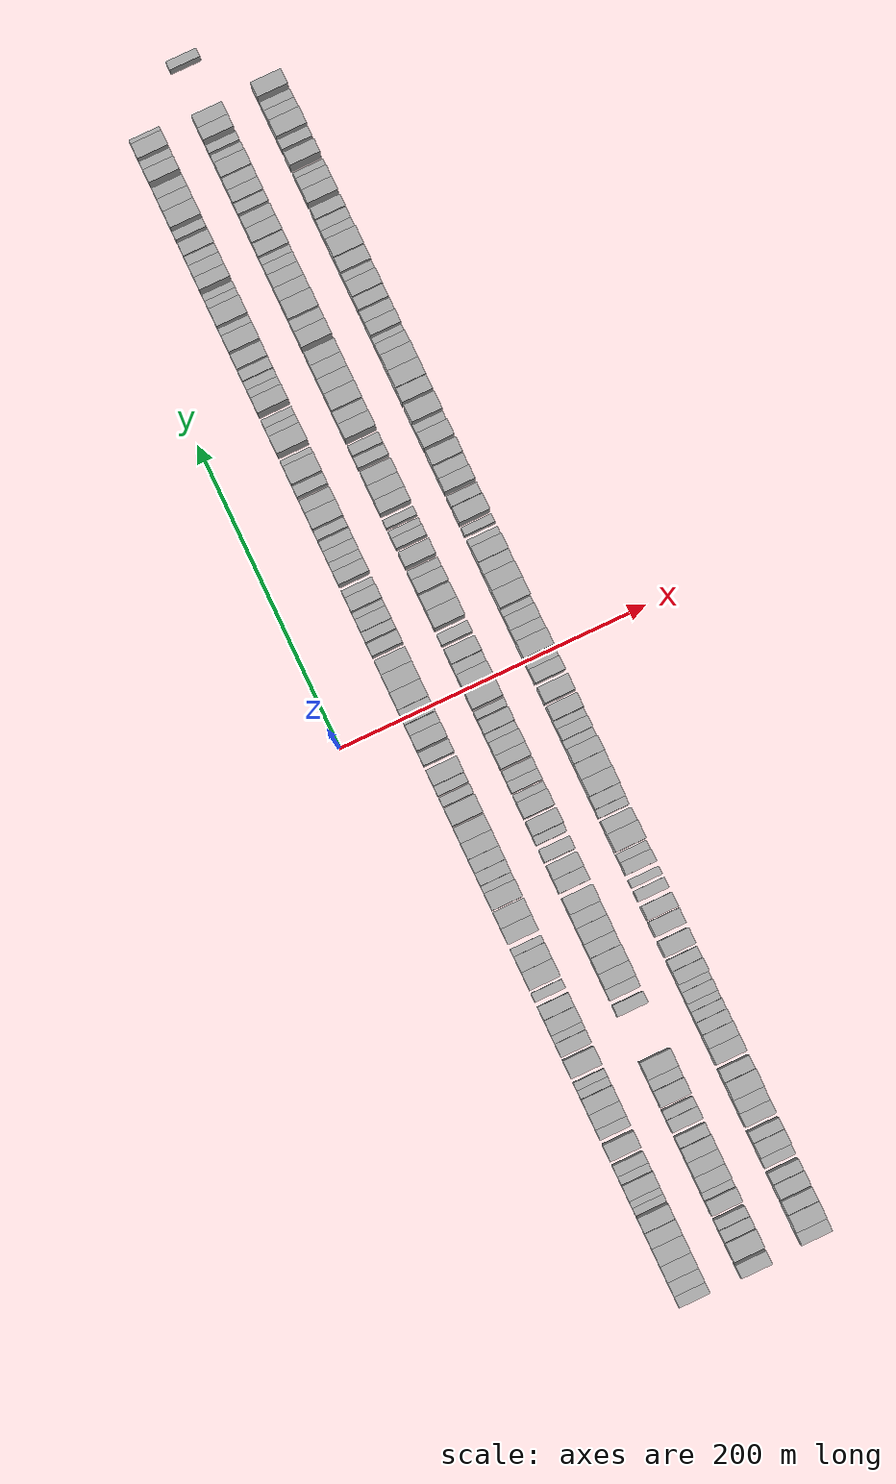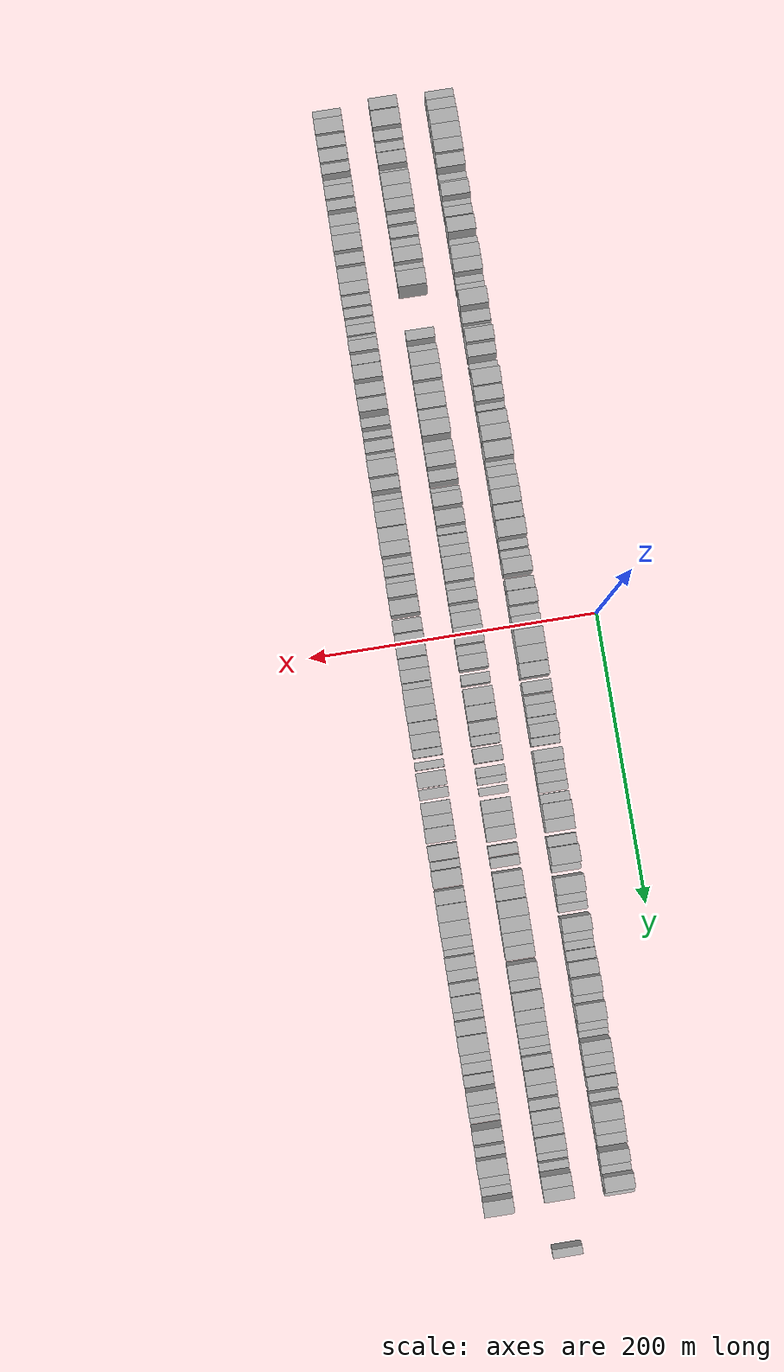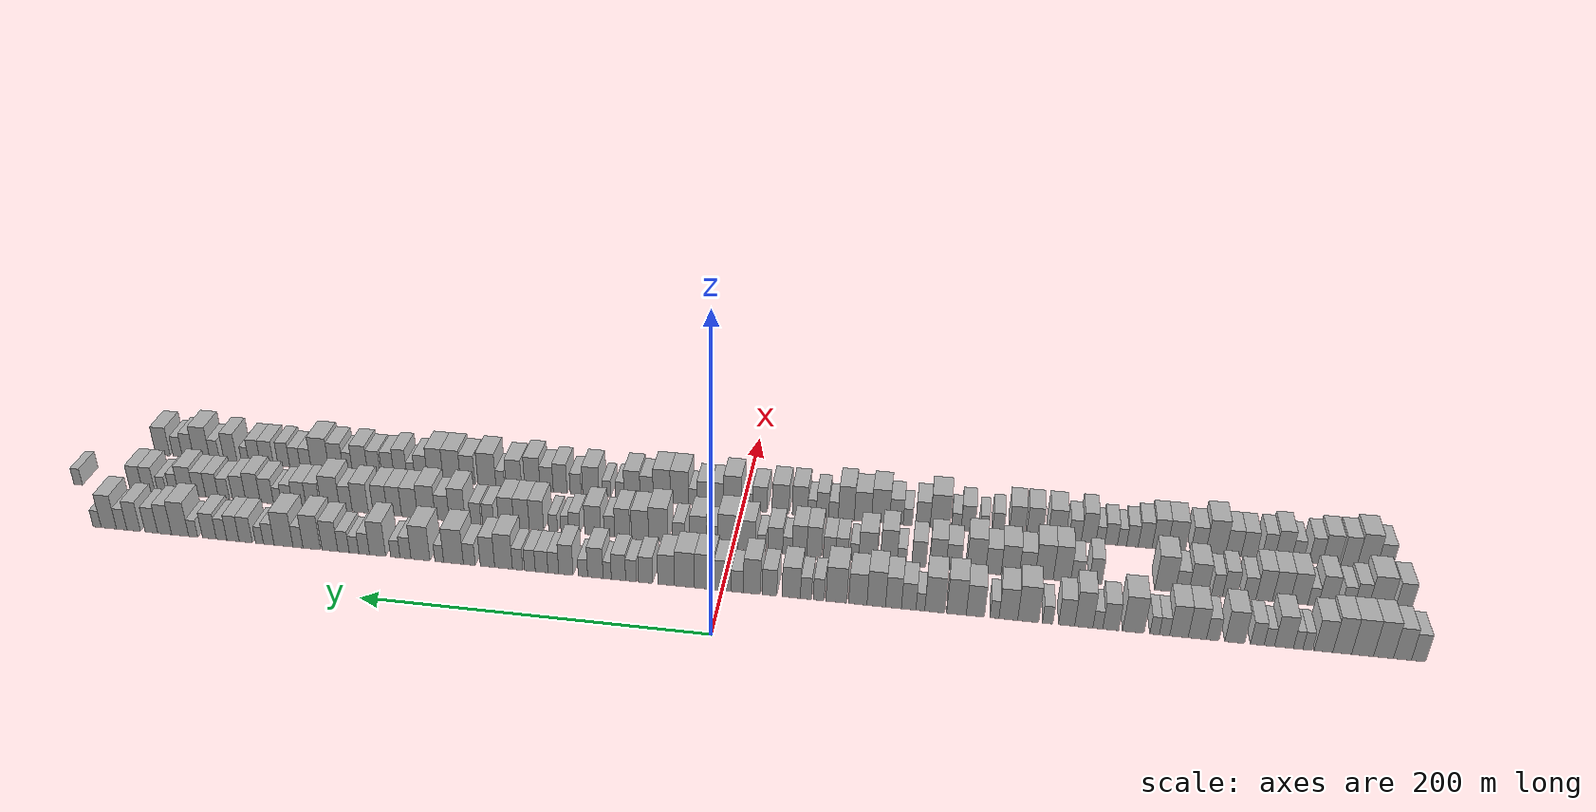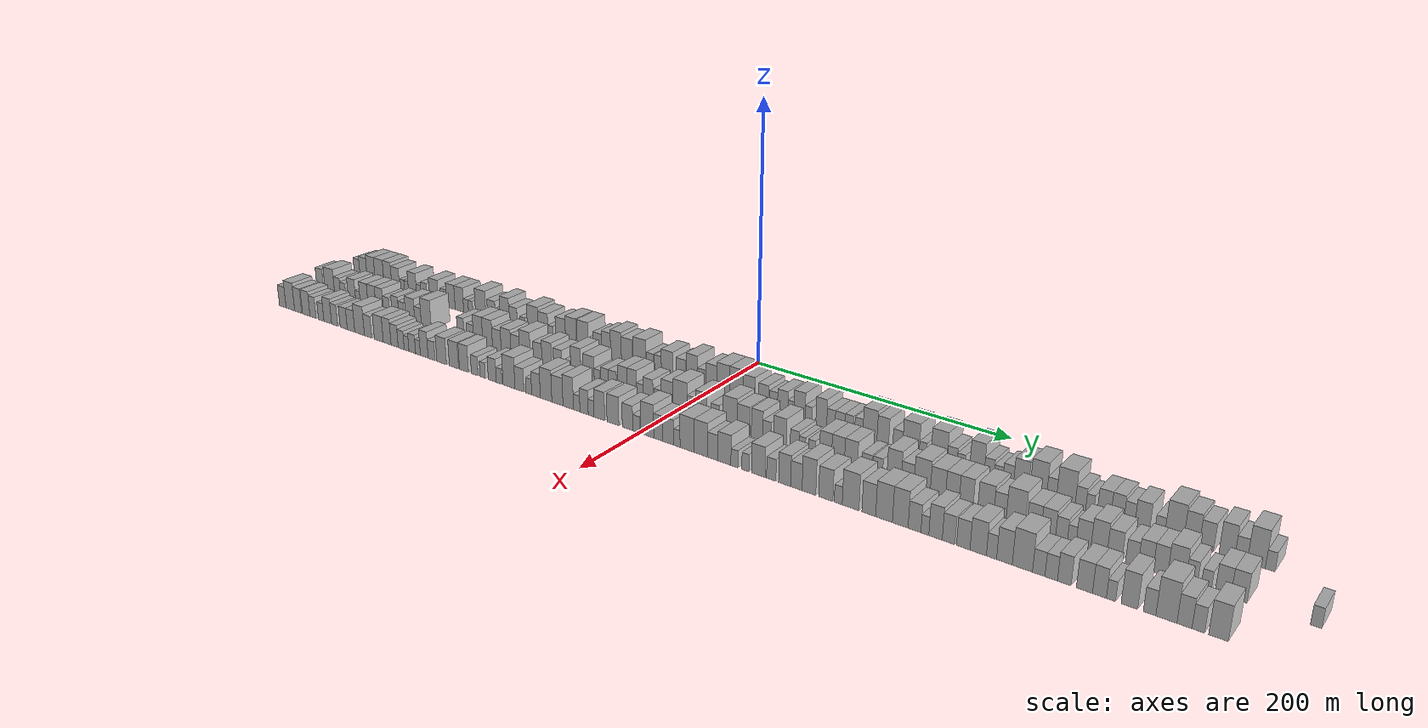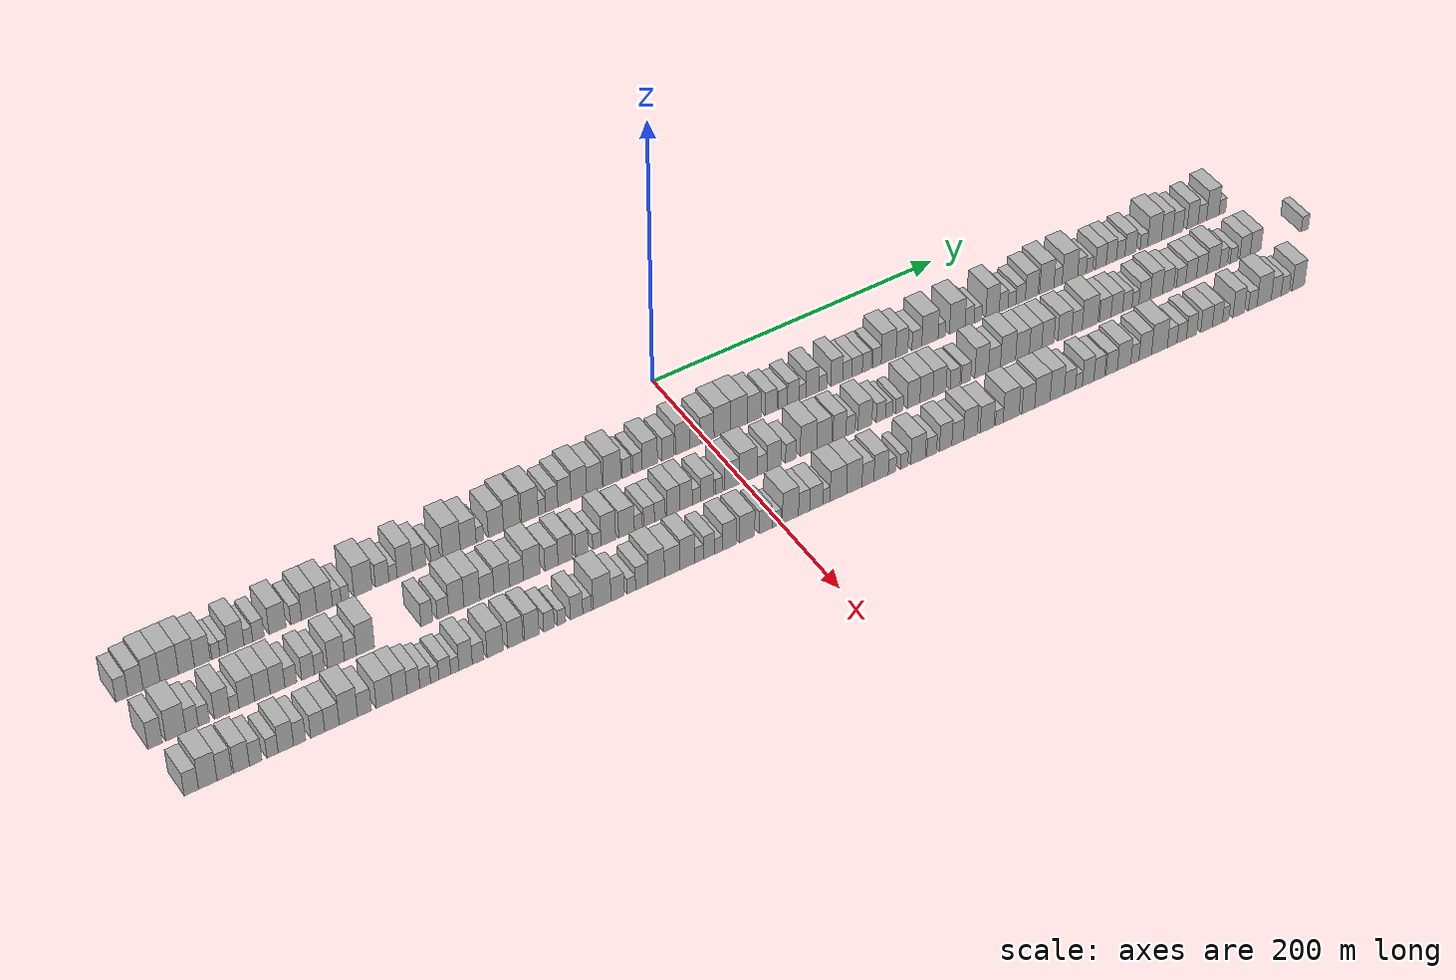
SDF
<sdf version="1.6">
 <world name="default">
  <scene>
   <sky><clouds><speed>12</speed></clouds></sky>
   <ambient>0.4 0.4 0.4 1</ambient>
   <background>0.7 0.7 0.7 1</background>
   <shadows>1</shadows>
  </scene>
  <gravity>0 0 -9.8066</gravity>
  <magnetic_field>6e-06 2.3e-05 -4.2e-05</magnetic_field>
  <physics default="0" name="default_physics" type="ode">
   <ode>
    <solver>
     <type>quick</type>
     <iters>10</iters>
     <sor>1.0</sor>
     <use_dynamic_moi_rescaling>0</use_dynamic_moi_rescaling>
    </solver>
    <constraints>
     <cfm>0</cfm>
     <erp>0.2</erp>
     <contact_max_correcting_vel>100</contact_max_correcting_vel>
     <contact_surface_layer>0.001</contact_surface_layer>
    </constraints>
   </ode>
   <max_step_size>0.004</max_step_size>
   <real_time_factor>1</real_time_factor>
   <real_time_update_rate>250</real_time_update_rate>
  </physics>
  <light name="sun" type="directional">
   <pose>0 0 10 0 0 0</pose>
   <diffuse>0.8 0.8 0.8 1</diffuse>
   <specular>0.2 0.2 0.2 1</specular>
   <attenuation>
    <range>1000</range>
    <constant>0.9</constant>
    <linear>0.01</linear>
    <quadratic>0.001</quadratic>
   </attenuation>
   <direction>-0.5 0.1 -0.9</direction>
  </light>
  <model name="building_1">
   <static>1</static>
   <pose>50.0000 -376.3061 0 0.000000 0.000000 0.000000</pose>
   <link name="link">
    <pose>0 0 9.00 0 0 0</pose>
    <collision name="collision"><geometry><box><size>20.0000 7.3878 18.0000</size></box></geometry></collision>
    <visual name="visual">
     <cast_shadows>0</cast_shadows>
     <geometry><box><size>20.0000 7.3878 18.0000</size></box></geometry>
     <material>
      <script>
       <uri>model://HANNAS_wall/materials/scripts</uri>
       <uri>model://HANNAS_wall/materials/textures</uri>
       <name>vrc/HANNAS_wall</name>
      </script>
     </material>
    </visual>
   </link>
  </model>
  <model name="building_2">
   <static>1</static>
   <pose>50.0000 -368.0308 0 0.000000 0.000000 0.000000</pose>
   <link name="link">
    <pose>0 0 10.50 0 0 0</pose>
    <collision name="collision"><geometry><box><size>20.0000 9.1627 21.0000</size></box></geometry></collision>
    <visual name="visual">
     <cast_shadows>0</cast_shadows>
     <geometry><box><size>20.0000 9.1627 21.0000</size></box></geometry>
     <material>
      <script>
       <uri>model://HANNAS_wall/materials/scripts</uri>
       <uri>model://HANNAS_wall/materials/textures</uri>
       <name>vrc/HANNAS_wall</name>
      </script>
     </material>
    </visual>
   </link>
  </model>
  <model name="building_3">
   <static>1</static>
   <pose>50.0000 -358.3713 0 0.000000 0.000000 0.000000</pose>
   <link name="link">
    <pose>0 0 12.00 0 0 0</pose>
    <collision name="collision"><geometry><box><size>20.0000 10.1564 24.0000</size></box></geometry></collision>
    <visual name="visual">
     <cast_shadows>0</cast_shadows>
     <geometry><box><size>20.0000 10.1564 24.0000</size></box></geometry>
     <material>
      <script>
       <uri>model://HANNAS_wall/materials/scripts</uri>
       <uri>model://HANNAS_wall/materials/textures</uri>
       <name>vrc/HANNAS_wall</name>
      </script>
     </material>
    </visual>
   </link>
  </model>
  <model name="building_4">
   <static>1</static>
   <pose>50.0000 -347.6701 0 0.000000 0.000000 0.000000</pose>
   <link name="link">
    <pose>0 0 12.00 0 0 0</pose>
    <collision name="collision"><geometry><box><size>20.0000 11.2460 24.0000</size></box></geometry></collision>
    <visual name="visual">
     <cast_shadows>0</cast_shadows>
     <geometry><box><size>20.0000 11.2460 24.0000</size></box></geometry>
     <material>
      <script>
       <uri>model://HANNAS_wall/materials/scripts</uri>
       <uri>model://HANNAS_wall/materials/textures</uri>
       <name>vrc/HANNAS_wall</name>
      </script>
     </material>
    </visual>
   </link>
  </model>
  <model name="building_5">
   <static>1</static>
   <pose>50.0000 -337.1962 0 0.000000 0.000000 0.000000</pose>
   <link name="link">
    <pose>0 0 12.00 0 0 0</pose>
    <collision name="collision"><geometry><box><size>20.0000 9.7019 24.0000</size></box></geometry></collision>
    <visual name="visual">
     <cast_shadows>0</cast_shadows>
     <geometry><box><size>20.0000 9.7019 24.0000</size></box></geometry>
     <material>
      <script>
       <uri>model://HANNAS_wall/materials/scripts</uri>
       <uri>model://HANNAS_wall/materials/textures</uri>
       <name>vrc/HANNAS_wall</name>
      </script>
     </material>
    </visual>
   </link>
  </model>
  <model name="building_6">
   <static>1</static>
   <pose>50.0000 -327.5208 0 0.000000 0.000000 0.000000</pose>
   <link name="link">
    <pose>0 0 10.50 0 0 0</pose>
    <collision name="collision"><geometry><box><size>20.0000 9.6488 21.0000</size></box></geometry></collision>
    <visual name="visual">
     <cast_shadows>0</cast_shadows>
     <geometry><box><size>20.0000 9.6488 21.0000</size></box></geometry>
     <material>
      <script>
       <uri>model://HANNAS_wall/materials/scripts</uri>
       <uri>model://HANNAS_wall/materials/textures</uri>
       <name>vrc/HANNAS_wall</name>
      </script>
     </material>
    </visual>
   </link>
  </model>
  <model name="building_7">
   <static>1</static>
   <pose>50.0000 -319.2568 0 0.000000 0.000000 0.000000</pose>
   <link name="link">
    <pose>0 0 6.00 0 0 0</pose>
    <collision name="collision"><geometry><box><size>20.0000 4.8792 12.0000</size></box></geometry></collision>
    <visual name="visual">
     <cast_shadows>0</cast_shadows>
     <geometry><box><size>20.0000 4.8792 12.0000</size></box></geometry>
     <material>
      <script>
       <uri>model://HANNAS_wall/materials/scripts</uri>
       <uri>model://HANNAS_wall/materials/textures</uri>
       <name>vrc/HANNAS_wall</name>
      </script>
     </material>
    </visual>
   </link>
  </model>
  <model name="building_8">
   <static>1</static>
   <pose>50.0000 -314.3427 0 0.000000 0.000000 0.000000</pose>
   <link name="link">
    <pose>0 0 6.00 0 0 0</pose>
    <collision name="collision"><geometry><box><size>20.0000 4.9490 12.0000</size></box></geometry></collision>
    <visual name="visual">
     <cast_shadows>0</cast_shadows>
     <geometry><box><size>20.0000 4.9490 12.0000</size></box></geometry>
     <material>
      <script>
       <uri>model://HANNAS_wall/materials/scripts</uri>
       <uri>model://HANNAS_wall/materials/textures</uri>
       <name>vrc/HANNAS_wall</name>
      </script>
     </material>
    </visual>
   </link>
  </model>
  <model name="building_9">
   <static>1</static>
   <pose>50.0000 -306.9284 0 0.000000 0.000000 0.000000</pose>
   <link name="link">
    <pose>0 0 10.50 0 0 0</pose>
    <collision name="collision"><geometry><box><size>20.0000 9.8796 21.0000</size></box></geometry></collision>
    <visual name="visual">
     <cast_shadows>0</cast_shadows>
     <geometry><box><size>20.0000 9.8796 21.0000</size></box></geometry>
     <material>
      <script>
       <uri>model://HANNAS_wall/materials/scripts</uri>
       <uri>model://HANNAS_wall/materials/textures</uri>
       <name>vrc/HANNAS_wall</name>
      </script>
     </material>
    </visual>
   </link>
  </model>
  <model name="building_10">
   <static>1</static>
   <pose>50.0000 -299.2899 0 0.000000 0.000000 0.000000</pose>
   <link name="link">
    <pose>0 0 6.00 0 0 0</pose>
    <collision name="collision"><geometry><box><size>20.0000 5.3975 12.0000</size></box></geometry></collision>
    <visual name="visual">
     <cast_shadows>0</cast_shadows>
     <geometry><box><size>20.0000 5.3975 12.0000</size></box></geometry>
     <material>
      <script>
       <uri>model://HANNAS_wall/materials/scripts</uri>
       <uri>model://HANNAS_wall/materials/textures</uri>
       <name>vrc/HANNAS_wall</name>
      </script>
     </material>
    </visual>
   </link>
  </model>
  <model name="building_11">
   <static>1</static>
   <pose>50.0000 -293.0411 0 0.000000 0.000000 0.000000</pose>
   <link name="link">
    <pose>0 0 7.50 0 0 0</pose>
    <collision name="collision"><geometry><box><size>20.0000 7.1000 15.0000</size></box></geometry></collision>
    <visual name="visual">
     <cast_shadows>0</cast_shadows>
     <geometry><box><size>20.0000 7.1000 15.0000</size></box></geometry>
     <material>
      <script>
       <uri>model://HANNAS_wall/materials/scripts</uri>
       <uri>model://HANNAS_wall/materials/textures</uri>
       <name>vrc/HANNAS_wall</name>
      </script>
     </material>
    </visual>
   </link>
  </model>
  <model name="building_12">
   <static>1</static>
   <pose>50.0000 -281.2441 0 0.000000 0.000000 0.000000</pose>
   <link name="link">
    <pose>0 0 10.50 0 0 0</pose>
    <collision name="collision"><geometry><box><size>20.0000 10.4942 21.0000</size></box></geometry></collision>
    <visual name="visual">
     <cast_shadows>0</cast_shadows>
     <geometry><box><size>20.0000 10.4942 21.0000</size></box></geometry>
     <material>
      <script>
       <uri>model://HANNAS_wall/materials/scripts</uri>
       <uri>model://HANNAS_wall/materials/textures</uri>
       <name>vrc/HANNAS_wall</name>
      </script>
     </material>
    </visual>
   </link>
  </model>
  <model name="building_13">
   <static>1</static>
   <pose>50.0000 -269.6385 0 0.000000 0.000000 0.000000</pose>
   <link name="link">
    <pose>0 0 7.50 0 0 0</pose>
    <collision name="collision"><geometry><box><size>20.0000 6.7169 15.0000</size></box></geometry></collision>
    <visual name="visual">
     <cast_shadows>0</cast_shadows>
     <geometry><box><size>20.0000 6.7169 15.0000</size></box></geometry>
     <material>
      <script>
       <uri>model://HANNAS_wall/materials/scripts</uri>
       <uri>model://HANNAS_wall/materials/textures</uri>
       <name>vrc/HANNAS_wall</name>
      </script>
     </material>
    </visual>
   </link>
  </model>
  <model name="building_14">
   <static>1</static>
   <pose>50.0000 -261.4667 0 0.000000 0.000000 0.000000</pose>
   <link name="link">
    <pose>0 0 10.50 0 0 0</pose>
    <collision name="collision"><geometry><box><size>20.0000 9.6268 21.0000</size></box></geometry></collision>
    <visual name="visual">
     <cast_shadows>0</cast_shadows>
     <geometry><box><size>20.0000 9.6268 21.0000</size></box></geometry>
     <material>
      <script>
       <uri>model://HANNAS_wall/materials/scripts</uri>
       <uri>model://HANNAS_wall/materials/textures</uri>
       <name>vrc/HANNAS_wall</name>
      </script>
     </material>
    </visual>
   </link>
  </model>
  <model name="building_15">
   <static>1</static>
   <pose>50.0000 -251.7313 0 0.000000 0.000000 0.000000</pose>
   <link name="link">
    <pose>0 0 10.50 0 0 0</pose>
    <collision name="collision"><geometry><box><size>20.0000 9.8440 21.0000</size></box></geometry></collision>
    <visual name="visual">
     <cast_shadows>0</cast_shadows>
     <geometry><box><size>20.0000 9.8440 21.0000</size></box></geometry>
     <material>
      <script>
       <uri>model://HANNAS_wall/materials/scripts</uri>
       <uri>model://HANNAS_wall/materials/textures</uri>
       <name>vrc/HANNAS_wall</name>
      </script>
     </material>
    </visual>
   </link>
  </model>
  <model name="building_16">
   <static>1</static>
   <pose>50.0000 -244.0632 0 0.000000 0.000000 0.000000</pose>
   <link name="link">
    <pose>0 0 6.00 0 0 0</pose>
    <collision name="collision"><geometry><box><size>20.0000 5.4923 12.0000</size></box></geometry></collision>
    <visual name="visual">
     <cast_shadows>0</cast_shadows>
     <geometry><box><size>20.0000 5.4923 12.0000</size></box></geometry>
     <material>
      <script>
       <uri>model://HANNAS_wall/materials/scripts</uri>
       <uri>model://HANNAS_wall/materials/textures</uri>
       <name>vrc/HANNAS_wall</name>
      </script>
     </material>
    </visual>
   </link>
  </model>
  <model name="building_17">
   <static>1</static>
   <pose>50.0000 -238.7936 0 0.000000 0.000000 0.000000</pose>
   <link name="link">
    <pose>0 0 6.00 0 0 0</pose>
    <collision name="collision"><geometry><box><size>20.0000 5.0470 12.0000</size></box></geometry></collision>
    <visual name="visual">
     <cast_shadows>0</cast_shadows>
     <geometry><box><size>20.0000 5.0470 12.0000</size></box></geometry>
     <material>
      <script>
       <uri>model://HANNAS_wall/materials/scripts</uri>
       <uri>model://HANNAS_wall/materials/textures</uri>
       <name>vrc/HANNAS_wall</name>
      </script>
     </material>
    </visual>
   </link>
  </model>
  <model name="building_18">
   <static>1</static>
   <pose>50.0000 -227.4646 0 0.000000 0.000000 0.000000</pose>
   <link name="link">
    <pose>0 0 12.00 0 0 0</pose>
    <collision name="collision"><geometry><box><size>20.0000 11.6110 24.0000</size></box></geometry></collision>
    <visual name="visual">
     <cast_shadows>0</cast_shadows>
     <geometry><box><size>20.0000 11.6110 24.0000</size></box></geometry>
     <material>
      <script>
       <uri>model://HANNAS_wall/materials/scripts</uri>
       <uri>model://HANNAS_wall/materials/textures</uri>
       <name>vrc/HANNAS_wall</name>
      </script>
     </material>
    </visual>
   </link>
  </model>
  <model name="building_19">
   <static>1</static>
   <pose>50.0000 -215.3501 0 0.000000 0.000000 0.000000</pose>
   <link name="link">
    <pose>0 0 9.00 0 0 0</pose>
    <collision name="collision"><geometry><box><size>20.0000 8.6180 18.0000</size></box></geometry></collision>
    <visual name="visual">
     <cast_shadows>0</cast_shadows>
     <geometry><box><size>20.0000 8.6180 18.0000</size></box></geometry>
     <material>
      <script>
       <uri>model://HANNAS_wall/materials/scripts</uri>
       <uri>model://HANNAS_wall/materials/textures</uri>
       <name>vrc/HANNAS_wall</name>
      </script>
     </material>
    </visual>
   </link>
  </model>
  <model name="building_20">
   <static>1</static>
   <pose>50.0000 -208.3999 0 0.000000 0.000000 0.000000</pose>
   <link name="link">
    <pose>0 0 6.00 0 0 0</pose>
    <collision name="collision"><geometry><box><size>20.0000 5.2822 12.0000</size></box></geometry></collision>
    <visual name="visual">
     <cast_shadows>0</cast_shadows>
     <geometry><box><size>20.0000 5.2822 12.0000</size></box></geometry>
     <material>
      <script>
       <uri>model://HANNAS_wall/materials/scripts</uri>
       <uri>model://HANNAS_wall/materials/textures</uri>
       <name>vrc/HANNAS_wall</name>
      </script>
     </material>
    </visual>
   </link>
  </model>
  <model name="building_21">
   <static>1</static>
   <pose>50.0000 -200.8549 0 0.000000 0.000000 0.000000</pose>
   <link name="link">
    <pose>0 0 12.00 0 0 0</pose>
    <collision name="collision"><geometry><box><size>20.0000 9.8079 24.0000</size></box></geometry></collision>
    <visual name="visual">
     <cast_shadows>0</cast_shadows>
     <geometry><box><size>20.0000 9.8079 24.0000</size></box></geometry>
     <material>
      <script>
       <uri>model://HANNAS_wall/materials/scripts</uri>
       <uri>model://HANNAS_wall/materials/textures</uri>
       <name>vrc/HANNAS_wall</name>
      </script>
     </material>
    </visual>
   </link>
  </model>
  <model name="building_22">
   <static>1</static>
   <pose>50.0000 -191.5766 0 0.000000 0.000000 0.000000</pose>
   <link name="link">
    <pose>0 0 9.00 0 0 0</pose>
    <collision name="collision"><geometry><box><size>20.0000 8.7487 18.0000</size></box></geometry></collision>
    <visual name="visual">
     <cast_shadows>0</cast_shadows>
     <geometry><box><size>20.0000 8.7487 18.0000</size></box></geometry>
     <material>
      <script>
       <uri>model://HANNAS_wall/materials/scripts</uri>
       <uri>model://HANNAS_wall/materials/textures</uri>
       <name>vrc/HANNAS_wall</name>
      </script>
     </material>
    </visual>
   </link>
  </model>
  <model name="building_23">
   <static>1</static>
   <pose>50.0000 -181.3504 0 0.000000 0.000000 0.000000</pose>
   <link name="link">
    <pose>0 0 6.00 0 0 0</pose>
    <collision name="collision"><geometry><box><size>20.0000 5.7038 12.0000</size></box></geometry></collision>
    <visual name="visual">
     <cast_shadows>0</cast_shadows>
     <geometry><box><size>20.0000 5.7038 12.0000</size></box></geometry>
     <material>
      <script>
       <uri>model://HANNAS_wall/materials/scripts</uri>
       <uri>model://HANNAS_wall/materials/textures</uri>
       <name>vrc/HANNAS_wall</name>
      </script>
     </material>
    </visual>
   </link>
  </model>
  <model name="building_24">
   <static>1</static>
   <pose>50.0000 -170.7666 0 0.000000 0.000000 0.000000</pose>
   <link name="link">
    <pose>0 0 12.00 0 0 0</pose>
    <collision name="collision"><geometry><box><size>20.0000 11.4638 24.0000</size></box></geometry></collision>
    <visual name="visual">
     <cast_shadows>0</cast_shadows>
     <geometry><box><size>20.0000 11.4638 24.0000</size></box></geometry>
     <material>
      <script>
       <uri>model://HANNAS_wall/materials/scripts</uri>
       <uri>model://HANNAS_wall/materials/textures</uri>
       <name>vrc/HANNAS_wall</name>
      </script>
     </material>
    </visual>
   </link>
  </model>
  <model name="building_25">
   <static>1</static>
   <pose>50.0000 -159.9259 0 0.000000 0.000000 0.000000</pose>
   <link name="link">
    <pose>0 0 10.50 0 0 0</pose>
    <collision name="collision"><geometry><box><size>20.0000 10.2175 21.0000</size></box></geometry></collision>
    <visual name="visual">
     <cast_shadows>0</cast_shadows>
     <geometry><box><size>20.0000 10.2175 21.0000</size></box></geometry>
     <material>
      <script>
       <uri>model://HANNAS_wall/materials/scripts</uri>
       <uri>model://HANNAS_wall/materials/textures</uri>
       <name>vrc/HANNAS_wall</name>
      </script>
     </material>
    </visual>
   </link>
  </model>
  <model name="building_26">
   <static>1</static>
   <pose>50.0000 -152.3563 0 0.000000 0.000000 0.000000</pose>
   <link name="link">
    <pose>0 0 6.00 0 0 0</pose>
    <collision name="collision"><geometry><box><size>20.0000 4.9218 12.0000</size></box></geometry></collision>
    <visual name="visual">
     <cast_shadows>0</cast_shadows>
     <geometry><box><size>20.0000 4.9218 12.0000</size></box></geometry>
     <material>
      <script>
       <uri>model://HANNAS_wall/materials/scripts</uri>
       <uri>model://HANNAS_wall/materials/textures</uri>
       <name>vrc/HANNAS_wall</name>
      </script>
     </material>
    </visual>
   </link>
  </model>
  <model name="building_27">
   <static>1</static>
   <pose>50.0000 -141.8743 0 0.000000 0.000000 0.000000</pose>
   <link name="link">
    <pose>0 0 10.50 0 0 0</pose>
    <collision name="collision"><geometry><box><size>20.0000 10.0421 21.0000</size></box></geometry></collision>
    <visual name="visual">
     <cast_shadows>0</cast_shadows>
     <geometry><box><size>20.0000 10.0421 21.0000</size></box></geometry>
     <material>
      <script>
       <uri>model://HANNAS_wall/materials/scripts</uri>
       <uri>model://HANNAS_wall/materials/textures</uri>
       <name>vrc/HANNAS_wall</name>
      </script>
     </material>
    </visual>
   </link>
  </model>
  <model name="building_28">
   <static>1</static>
   <pose>50.0000 -131.4665 0 0.000000 0.000000 0.000000</pose>
   <link name="link">
    <pose>0 0 12.00 0 0 0</pose>
    <collision name="collision"><geometry><box><size>20.0000 10.7736 24.0000</size></box></geometry></collision>
    <visual name="visual">
     <cast_shadows>0</cast_shadows>
     <geometry><box><size>20.0000 10.7736 24.0000</size></box></geometry>
     <material>
      <script>
       <uri>model://HANNAS_wall/materials/scripts</uri>
       <uri>model://HANNAS_wall/materials/textures</uri>
       <name>vrc/HANNAS_wall</name>
      </script>
     </material>
    </visual>
   </link>
  </model>
  <model name="building_29">
   <static>1</static>
   <pose>50.0000 -119.5319 0 0.000000 0.000000 0.000000</pose>
   <link name="link">
    <pose>0 0 12.00 0 0 0</pose>
    <collision name="collision"><geometry><box><size>20.0000 11.0957 24.0000</size></box></geometry></collision>
    <visual name="visual">
     <cast_shadows>0</cast_shadows>
     <geometry><box><size>20.0000 11.0957 24.0000</size></box></geometry>
     <material>
      <script>
       <uri>model://HANNAS_wall/materials/scripts</uri>
       <uri>model://HANNAS_wall/materials/textures</uri>
       <name>vrc/HANNAS_wall</name>
      </script>
     </material>
    </visual>
   </link>
  </model>
  <model name="building_30">
   <static>1</static>
   <pose>50.0000 -111.5464 0 0.000000 0.000000 0.000000</pose>
   <link name="link">
    <pose>0 0 6.00 0 0 0</pose>
    <collision name="collision"><geometry><box><size>20.0000 4.8752 12.0000</size></box></geometry></collision>
    <visual name="visual">
     <cast_shadows>0</cast_shadows>
     <geometry><box><size>20.0000 4.8752 12.0000</size></box></geometry>
     <material>
      <script>
       <uri>model://HANNAS_wall/materials/scripts</uri>
       <uri>model://HANNAS_wall/materials/textures</uri>
       <name>vrc/HANNAS_wall</name>
      </script>
     </material>
    </visual>
   </link>
  </model>
  <model name="building_31">
   <static>1</static>
   <pose>50.0000 -105.0671 0 0.000000 0.000000 0.000000</pose>
   <link name="link">
    <pose>0 0 9.00 0 0 0</pose>
    <collision name="collision"><geometry><box><size>20.0000 8.0835 18.0000</size></box></geometry></collision>
    <visual name="visual">
     <cast_shadows>0</cast_shadows>
     <geometry><box><size>20.0000 8.0835 18.0000</size></box></geometry>
     <material>
      <script>
       <uri>model://HANNAS_wall/materials/scripts</uri>
       <uri>model://HANNAS_wall/materials/textures</uri>
       <name>vrc/HANNAS_wall</name>
      </script>
     </material>
    </visual>
   </link>
  </model>
  <model name="building_32">
   <static>1</static>
   <pose>50.0000 -96.6124 0 0.000000 0.000000 0.000000</pose>
   <link name="link">
    <pose>0 0 10.50 0 0 0</pose>
    <collision name="collision"><geometry><box><size>20.0000 8.8259 21.0000</size></box></geometry></collision>
    <visual name="visual">
     <cast_shadows>0</cast_shadows>
     <geometry><box><size>20.0000 8.8259 21.0000</size></box></geometry>
     <material>
      <script>
       <uri>model://HANNAS_wall/materials/scripts</uri>
       <uri>model://HANNAS_wall/materials/textures</uri>
       <name>vrc/HANNAS_wall</name>
      </script>
     </material>
    </visual>
   </link>
  </model>
  <model name="building_33">
   <static>1</static>
   <pose>50.0000 -87.0101 0 0.000000 0.000000 0.000000</pose>
   <link name="link">
    <pose>0 0 12.00 0 0 0</pose>
    <collision name="collision"><geometry><box><size>20.0000 10.3787 24.0000</size></box></geometry></collision>
    <visual name="visual">
     <cast_shadows>0</cast_shadows>
     <geometry><box><size>20.0000 10.3787 24.0000</size></box></geometry>
     <material>
      <script>
       <uri>model://HANNAS_wall/materials/scripts</uri>
       <uri>model://HANNAS_wall/materials/textures</uri>
       <name>vrc/HANNAS_wall</name>
      </script>
     </material>
    </visual>
   </link>
  </model>
  <model name="building_34">
   <static>1</static>
   <pose>50.0000 -76.6844 0 0.000000 0.000000 0.000000</pose>
   <link name="link">
    <pose>0 0 10.50 0 0 0</pose>
    <collision name="collision"><geometry><box><size>20.0000 10.2727 21.0000</size></box></geometry></collision>
    <visual name="visual">
     <cast_shadows>0</cast_shadows>
     <geometry><box><size>20.0000 10.2727 21.0000</size></box></geometry>
     <material>
      <script>
       <uri>model://HANNAS_wall/materials/scripts</uri>
       <uri>model://HANNAS_wall/materials/textures</uri>
       <name>vrc/HANNAS_wall</name>
      </script>
     </material>
    </visual>
   </link>
  </model>
  <model name="building_35">
   <static>1</static>
   <pose>50.0000 -64.6732 0 0.000000 0.000000 0.000000</pose>
   <link name="link">
    <pose>0 0 12.00 0 0 0</pose>
    <collision name="collision"><geometry><box><size>20.0000 11.7496 24.0000</size></box></geometry></collision>
    <visual name="visual">
     <cast_shadows>0</cast_shadows>
     <geometry><box><size>20.0000 11.7496 24.0000</size></box></geometry>
     <material>
      <script>
       <uri>model://HANNAS_wall/materials/scripts</uri>
       <uri>model://HANNAS_wall/materials/textures</uri>
       <name>vrc/HANNAS_wall</name>
      </script>
     </material>
    </visual>
   </link>
  </model>
  <model name="building_36">
   <static>1</static>
   <pose>50.0000 -54.7265 0 0.000000 0.000000 0.000000</pose>
   <link name="link">
    <pose>0 0 7.50 0 0 0</pose>
    <collision name="collision"><geometry><box><size>20.0000 6.1438 15.0000</size></box></geometry></collision>
    <visual name="visual">
     <cast_shadows>0</cast_shadows>
     <geometry><box><size>20.0000 6.1438 15.0000</size></box></geometry>
     <material>
      <script>
       <uri>model://HANNAS_wall/materials/scripts</uri>
       <uri>model://HANNAS_wall/materials/textures</uri>
       <name>vrc/HANNAS_wall</name>
      </script>
     </material>
    </visual>
   </link>
  </model>
  <model name="building_37">
   <static>1</static>
   <pose>50.0000 -47.5194 0 0.000000 0.000000 0.000000</pose>
   <link name="link">
    <pose>0 0 7.50 0 0 0</pose>
    <collision name="collision"><geometry><box><size>20.0000 6.2705 15.0000</size></box></geometry></collision>
    <visual name="visual">
     <cast_shadows>0</cast_shadows>
     <geometry><box><size>20.0000 6.2705 15.0000</size></box></geometry>
     <material>
      <script>
       <uri>model://HANNAS_wall/materials/scripts</uri>
       <uri>model://HANNAS_wall/materials/textures</uri>
       <name>vrc/HANNAS_wall</name>
      </script>
     </material>
    </visual>
   </link>
  </model>
  <model name="building_38">
   <static>1</static>
   <pose>50.0000 -39.1840 0 0.000000 0.000000 0.000000</pose>
   <link name="link">
    <pose>0 0 10.50 0 0 0</pose>
    <collision name="collision"><geometry><box><size>20.0000 10.4003 21.0000</size></box></geometry></collision>
    <visual name="visual">
     <cast_shadows>0</cast_shadows>
     <geometry><box><size>20.0000 10.4003 21.0000</size></box></geometry>
     <material>
      <script>
       <uri>model://HANNAS_wall/materials/scripts</uri>
       <uri>model://HANNAS_wall/materials/textures</uri>
       <name>vrc/HANNAS_wall</name>
      </script>
     </material>
    </visual>
   </link>
  </model>
  <model name="building_39">
   <static>1</static>
   <pose>50.0000 -26.8468 0 0.000000 0.000000 0.000000</pose>
   <link name="link">
    <pose>0 0 9.00 0 0 0</pose>
    <collision name="collision"><geometry><box><size>20.0000 8.2742 18.0000</size></box></geometry></collision>
    <visual name="visual">
     <cast_shadows>0</cast_shadows>
     <geometry><box><size>20.0000 8.2742 18.0000</size></box></geometry>
     <material>
      <script>
       <uri>model://HANNAS_wall/materials/scripts</uri>
       <uri>model://HANNAS_wall/materials/textures</uri>
       <name>vrc/HANNAS_wall</name>
      </script>
     </material>
    </visual>
   </link>
  </model>
  <model name="building_40">
   <static>1</static>
   <pose>50.0000 -16.8517 0 0.000000 0.000000 0.000000</pose>
   <link name="link">
    <pose>0 0 12.00 0 0 0</pose>
    <collision name="collision"><geometry><box><size>20.0000 9.7160 24.0000</size></box></geometry></collision>
    <visual name="visual">
     <cast_shadows>0</cast_shadows>
     <geometry><box><size>20.0000 9.7160 24.0000</size></box></geometry>
     <material>
      <script>
       <uri>model://HANNAS_wall/materials/scripts</uri>
       <uri>model://HANNAS_wall/materials/textures</uri>
       <name>vrc/HANNAS_wall</name>
      </script>
     </material>
    </visual>
   </link>
  </model>
  <model name="building_41">
   <static>1</static>
   <pose>50.0000 -8.3444 0 0.000000 0.000000 0.000000</pose>
   <link name="link">
    <pose>0 0 7.50 0 0 0</pose>
    <collision name="collision"><geometry><box><size>20.0000 7.2987 15.0000</size></box></geometry></collision>
    <visual name="visual">
     <cast_shadows>0</cast_shadows>
     <geometry><box><size>20.0000 7.2987 15.0000</size></box></geometry>
     <material>
      <script>
       <uri>model://HANNAS_wall/materials/scripts</uri>
       <uri>model://HANNAS_wall/materials/textures</uri>
       <name>vrc/HANNAS_wall</name>
      </script>
     </material>
    </visual>
   </link>
  </model>
  <model name="building_42">
   <static>1</static>
   <pose>50.0000 0.0549 0 0.000000 0.000000 0.000000</pose>
   <link name="link">
    <pose>0 0 10.50 0 0 0</pose>
    <collision name="collision"><geometry><box><size>20.0000 9.4999 21.0000</size></box></geometry></collision>
    <visual name="visual">
     <cast_shadows>0</cast_shadows>
     <geometry><box><size>20.0000 9.4999 21.0000</size></box></geometry>
     <material>
      <script>
       <uri>model://HANNAS_wall/materials/scripts</uri>
       <uri>model://HANNAS_wall/materials/textures</uri>
       <name>vrc/HANNAS_wall</name>
      </script>
     </material>
    </visual>
   </link>
  </model>
  <model name="building_43">
   <static>1</static>
   <pose>50.0000 10.4526 0 0.000000 0.000000 0.000000</pose>
   <link name="link">
    <pose>0 0 12.00 0 0 0</pose>
    <collision name="collision"><geometry><box><size>20.0000 11.2954 24.0000</size></box></geometry></collision>
    <visual name="visual">
     <cast_shadows>0</cast_shadows>
     <geometry><box><size>20.0000 11.2954 24.0000</size></box></geometry>
     <material>
      <script>
       <uri>model://HANNAS_wall/materials/scripts</uri>
       <uri>model://HANNAS_wall/materials/textures</uri>
       <name>vrc/HANNAS_wall</name>
      </script>
     </material>
    </visual>
   </link>
  </model>
  <model name="building_44">
   <static>1</static>
   <pose>50.0000 21.8897 0 0.000000 0.000000 0.000000</pose>
   <link name="link">
    <pose>0 0 12.00 0 0 0</pose>
    <collision name="collision"><geometry><box><size>20.0000 11.5788 24.0000</size></box></geometry></collision>
    <visual name="visual">
     <cast_shadows>0</cast_shadows>
     <geometry><box><size>20.0000 11.5788 24.0000</size></box></geometry>
     <material>
      <script>
       <uri>model://HANNAS_wall/materials/scripts</uri>
       <uri>model://HANNAS_wall/materials/textures</uri>
       <name>vrc/HANNAS_wall</name>
      </script>
     </material>
    </visual>
   </link>
  </model>
  <model name="building_45">
   <static>1</static>
   <pose>50.0000 32.5011 0 0.000000 0.000000 0.000000</pose>
   <link name="link">
    <pose>0 0 10.50 0 0 0</pose>
    <collision name="collision"><geometry><box><size>20.0000 9.6440 21.0000</size></box></geometry></collision>
    <visual name="visual">
     <cast_shadows>0</cast_shadows>
     <geometry><box><size>20.0000 9.6440 21.0000</size></box></geometry>
     <material>
      <script>
       <uri>model://HANNAS_wall/materials/scripts</uri>
       <uri>model://HANNAS_wall/materials/textures</uri>
       <name>vrc/HANNAS_wall</name>
      </script>
     </material>
    </visual>
   </link>
  </model>
  <model name="building_46">
   <static>1</static>
   <pose>50.0000 44.4527 0 0.000000 0.000000 0.000000</pose>
   <link name="link">
    <pose>0 0 9.00 0 0 0</pose>
    <collision name="collision"><geometry><box><size>20.0000 8.2592 18.0000</size></box></geometry></collision>
    <visual name="visual">
     <cast_shadows>0</cast_shadows>
     <geometry><box><size>20.0000 8.2592 18.0000</size></box></geometry>
     <material>
      <script>
       <uri>model://HANNAS_wall/materials/scripts</uri>
       <uri>model://HANNAS_wall/materials/textures</uri>
       <name>vrc/HANNAS_wall</name>
      </script>
     </material>
    </visual>
   </link>
  </model>
  <model name="building_47">
   <static>1</static>
   <pose>50.0000 52.7988 0 0.000000 0.000000 0.000000</pose>
   <link name="link">
    <pose>0 0 7.50 0 0 0</pose>
    <collision name="collision"><geometry><box><size>20.0000 6.4331 15.0000</size></box></geometry></collision>
    <visual name="visual">
     <cast_shadows>0</cast_shadows>
     <geometry><box><size>20.0000 6.4331 15.0000</size></box></geometry>
     <material>
      <script>
       <uri>model://HANNAS_wall/materials/scripts</uri>
       <uri>model://HANNAS_wall/materials/textures</uri>
       <name>vrc/HANNAS_wall</name>
      </script>
     </material>
    </visual>
   </link>
  </model>
  <model name="building_48">
   <static>1</static>
   <pose>50.0000 60.1944 0 0.000000 0.000000 0.000000</pose>
   <link name="link">
    <pose>0 0 9.00 0 0 0</pose>
    <collision name="collision"><geometry><box><size>20.0000 8.3580 18.0000</size></box></geometry></collision>
    <visual name="visual">
     <cast_shadows>0</cast_shadows>
     <geometry><box><size>20.0000 8.3580 18.0000</size></box></geometry>
     <material>
      <script>
       <uri>model://HANNAS_wall/materials/scripts</uri>
       <uri>model://HANNAS_wall/materials/textures</uri>
       <name>vrc/HANNAS_wall</name>
      </script>
     </material>
    </visual>
   </link>
  </model>
  <model name="building_49">
   <static>1</static>
   <pose>50.0000 66.7749 0 0.000000 0.000000 0.000000</pose>
   <link name="link">
    <pose>0 0 6.00 0 0 0</pose>
    <collision name="collision"><geometry><box><size>20.0000 4.8031 12.0000</size></box></geometry></collision>
    <visual name="visual">
     <cast_shadows>0</cast_shadows>
     <geometry><box><size>20.0000 4.8031 12.0000</size></box></geometry>
     <material>
      <script>
       <uri>model://HANNAS_wall/materials/scripts</uri>
       <uri>model://HANNAS_wall/materials/textures</uri>
       <name>vrc/HANNAS_wall</name>
      </script>
     </material>
    </visual>
   </link>
  </model>
  <model name="building_50">
   <static>1</static>
   <pose>50.0000 73.7119 0 0.000000 0.000000 0.000000</pose>
   <link name="link">
    <pose>0 0 10.50 0 0 0</pose>
    <collision name="collision"><geometry><box><size>20.0000 9.0707 21.0000</size></box></geometry></collision>
    <visual name="visual">
     <cast_shadows>0</cast_shadows>
     <geometry><box><size>20.0000 9.0707 21.0000</size></box></geometry>
     <material>
      <script>
       <uri>model://HANNAS_wall/materials/scripts</uri>
       <uri>model://HANNAS_wall/materials/textures</uri>
       <name>vrc/HANNAS_wall</name>
      </script>
     </material>
    </visual>
   </link>
  </model>
  <model name="building_51">
   <static>1</static>
   <pose>50.0000 81.0116 0 0.000000 0.000000 0.000000</pose>
   <link name="link">
    <pose>0 0 6.00 0 0 0</pose>
    <collision name="collision"><geometry><box><size>20.0000 5.5287 12.0000</size></box></geometry></collision>
    <visual name="visual">
     <cast_shadows>0</cast_shadows>
     <geometry><box><size>20.0000 5.5287 12.0000</size></box></geometry>
     <material>
      <script>
       <uri>model://HANNAS_wall/materials/scripts</uri>
       <uri>model://HANNAS_wall/materials/textures</uri>
       <name>vrc/HANNAS_wall</name>
      </script>
     </material>
    </visual>
   </link>
  </model>
  <model name="building_52">
   <static>1</static>
   <pose>50.0000 91.0099 0 0.000000 0.000000 0.000000</pose>
   <link name="link">
    <pose>0 0 10.50 0 0 0</pose>
    <collision name="collision"><geometry><box><size>20.0000 8.4680 21.0000</size></box></geometry></collision>
    <visual name="visual">
     <cast_shadows>0</cast_shadows>
     <geometry><box><size>20.0000 8.4680 21.0000</size></box></geometry>
     <material>
      <script>
       <uri>model://HANNAS_wall/materials/scripts</uri>
       <uri>model://HANNAS_wall/materials/textures</uri>
       <name>vrc/HANNAS_wall</name>
      </script>
     </material>
    </visual>
   </link>
  </model>
  <model name="building_53">
   <static>1</static>
   <pose>50.0000 98.4394 0 0.000000 0.000000 0.000000</pose>
   <link name="link">
    <pose>0 0 7.50 0 0 0</pose>
    <collision name="collision"><geometry><box><size>20.0000 6.3912 15.0000</size></box></geometry></collision>
    <visual name="visual">
     <cast_shadows>0</cast_shadows>
     <geometry><box><size>20.0000 6.3912 15.0000</size></box></geometry>
     <material>
      <script>
       <uri>model://HANNAS_wall/materials/scripts</uri>
       <uri>model://HANNAS_wall/materials/textures</uri>
       <name>vrc/HANNAS_wall</name>
      </script>
     </material>
    </visual>
   </link>
  </model>
  <model name="building_54">
   <static>1</static>
   <pose>50.0000 105.3752 0 0.000000 0.000000 0.000000</pose>
   <link name="link">
    <pose>0 0 7.50 0 0 0</pose>
    <collision name="collision"><geometry><box><size>20.0000 7.4803 15.0000</size></box></geometry></collision>
    <visual name="visual">
     <cast_shadows>0</cast_shadows>
     <geometry><box><size>20.0000 7.4803 15.0000</size></box></geometry>
     <material>
      <script>
       <uri>model://HANNAS_wall/materials/scripts</uri>
       <uri>model://HANNAS_wall/materials/textures</uri>
       <name>vrc/HANNAS_wall</name>
      </script>
     </material>
    </visual>
   </link>
  </model>
  <model name="building_55">
   <static>1</static>
   <pose>50.0000 112.3379 0 0.000000 0.000000 0.000000</pose>
   <link name="link">
    <pose>0 0 7.50 0 0 0</pose>
    <collision name="collision"><geometry><box><size>20.0000 6.4452 15.0000</size></box></geometry></collision>
    <visual name="visual">
     <cast_shadows>0</cast_shadows>
     <geometry><box><size>20.0000 6.4452 15.0000</size></box></geometry>
     <material>
      <script>
       <uri>model://HANNAS_wall/materials/scripts</uri>
       <uri>model://HANNAS_wall/materials/textures</uri>
       <name>vrc/HANNAS_wall</name>
      </script>
     </material>
    </visual>
   </link>
  </model>
  <model name="building_56">
   <static>1</static>
   <pose>50.0000 119.6325 0 0.000000 0.000000 0.000000</pose>
   <link name="link">
    <pose>0 0 7.50 0 0 0</pose>
    <collision name="collision"><geometry><box><size>20.0000 6.1440 15.0000</size></box></geometry></collision>
    <visual name="visual">
     <cast_shadows>0</cast_shadows>
     <geometry><box><size>20.0000 6.1440 15.0000</size></box></geometry>
     <material>
      <script>
       <uri>model://HANNAS_wall/materials/scripts</uri>
       <uri>model://HANNAS_wall/materials/textures</uri>
       <name>vrc/HANNAS_wall</name>
      </script>
     </material>
    </visual>
   </link>
  </model>
  <model name="building_57">
   <static>1</static>
   <pose>50.0000 128.0010 0 0.000000 0.000000 0.000000</pose>
   <link name="link">
    <pose>0 0 12.00 0 0 0</pose>
    <collision name="collision"><geometry><box><size>20.0000 10.5930 24.0000</size></box></geometry></collision>
    <visual name="visual">
     <cast_shadows>0</cast_shadows>
     <geometry><box><size>20.0000 10.5930 24.0000</size></box></geometry>
     <material>
      <script>
       <uri>model://HANNAS_wall/materials/scripts</uri>
       <uri>model://HANNAS_wall/materials/textures</uri>
       <name>vrc/HANNAS_wall</name>
      </script>
     </material>
    </visual>
   </link>
  </model>
  <model name="building_58">
   <static>1</static>
   <pose>50.0000 137.6000 0 0.000000 0.000000 0.000000</pose>
   <link name="link">
    <pose>0 0 10.50 0 0 0</pose>
    <collision name="collision"><geometry><box><size>20.0000 8.6049 21.0000</size></box></geometry></collision>
    <visual name="visual">
     <cast_shadows>0</cast_shadows>
     <geometry><box><size>20.0000 8.6049 21.0000</size></box></geometry>
     <material>
      <script>
       <uri>model://HANNAS_wall/materials/scripts</uri>
       <uri>model://HANNAS_wall/materials/textures</uri>
       <name>vrc/HANNAS_wall</name>
      </script>
     </material>
    </visual>
   </link>
  </model>
  <model name="building_59">
   <static>1</static>
   <pose>50.0000 148.4644 0 0.000000 0.000000 0.000000</pose>
   <link name="link">
    <pose>0 0 7.50 0 0 0</pose>
    <collision name="collision"><geometry><box><size>20.0000 7.1239 15.0000</size></box></geometry></collision>
    <visual name="visual">
     <cast_shadows>0</cast_shadows>
     <geometry><box><size>20.0000 7.1239 15.0000</size></box></geometry>
     <material>
      <script>
       <uri>model://HANNAS_wall/materials/scripts</uri>
       <uri>model://HANNAS_wall/materials/textures</uri>
       <name>vrc/HANNAS_wall</name>
      </script>
     </material>
    </visual>
   </link>
  </model>
  <model name="building_60">
   <static>1</static>
   <pose>50.0000 157.9762 0 0.000000 0.000000 0.000000</pose>
   <link name="link">
    <pose>0 0 12.00 0 0 0</pose>
    <collision name="collision"><geometry><box><size>20.0000 11.8997 24.0000</size></box></geometry></collision>
    <visual name="visual">
     <cast_shadows>0</cast_shadows>
     <geometry><box><size>20.0000 11.8997 24.0000</size></box></geometry>
     <material>
      <script>
       <uri>model://HANNAS_wall/materials/scripts</uri>
       <uri>model://HANNAS_wall/materials/textures</uri>
       <name>vrc/HANNAS_wall</name>
      </script>
     </material>
    </visual>
   </link>
  </model>
  <model name="building_61">
   <static>1</static>
   <pose>50.0000 166.5646 0 0.000000 0.000000 0.000000</pose>
   <link name="link">
    <pose>0 0 6.00 0 0 0</pose>
    <collision name="collision"><geometry><box><size>20.0000 5.2772 12.0000</size></box></geometry></collision>
    <visual name="visual">
     <cast_shadows>0</cast_shadows>
     <geometry><box><size>20.0000 5.2772 12.0000</size></box></geometry>
     <material>
      <script>
       <uri>model://HANNAS_wall/materials/scripts</uri>
       <uri>model://HANNAS_wall/materials/textures</uri>
       <name>vrc/HANNAS_wall</name>
      </script>
     </material>
    </visual>
   </link>
  </model>
  <model name="building_62">
   <static>1</static>
   <pose>50.0000 177.9136 0 0.000000 0.000000 0.000000</pose>
   <link name="link">
    <pose>0 0 12.00 0 0 0</pose>
    <collision name="collision"><geometry><box><size>20.0000 11.4206 24.0000</size></box></geometry></collision>
    <visual name="visual">
     <cast_shadows>0</cast_shadows>
     <geometry><box><size>20.0000 11.4206 24.0000</size></box></geometry>
     <material>
      <script>
       <uri>model://HANNAS_wall/materials/scripts</uri>
       <uri>model://HANNAS_wall/materials/textures</uri>
       <name>vrc/HANNAS_wall</name>
      </script>
     </material>
    </visual>
   </link>
  </model>
  <model name="building_63">
   <static>1</static>
   <pose>50.0000 186.9711 0 0.000000 0.000000 0.000000</pose>
   <link name="link">
    <pose>0 0 7.50 0 0 0</pose>
    <collision name="collision"><geometry><box><size>20.0000 6.6943 15.0000</size></box></geometry></collision>
    <visual name="visual">
     <cast_shadows>0</cast_shadows>
     <geometry><box><size>20.0000 6.6943 15.0000</size></box></geometry>
     <material>
      <script>
       <uri>model://HANNAS_wall/materials/scripts</uri>
       <uri>model://HANNAS_wall/materials/textures</uri>
       <name>vrc/HANNAS_wall</name>
      </script>
     </material>
    </visual>
   </link>
  </model>
  <model name="building_64">
   <static>1</static>
   <pose>50.0000 193.1554 0 0.000000 0.000000 0.000000</pose>
   <link name="link">
    <pose>0 0 6.00 0 0 0</pose>
    <collision name="collision"><geometry><box><size>20.0000 5.6743 12.0000</size></box></geometry></collision>
    <visual name="visual">
     <cast_shadows>0</cast_shadows>
     <geometry><box><size>20.0000 5.6743 12.0000</size></box></geometry>
     <material>
      <script>
       <uri>model://HANNAS_wall/materials/scripts</uri>
       <uri>model://HANNAS_wall/materials/textures</uri>
       <name>vrc/HANNAS_wall</name>
      </script>
     </material>
    </visual>
   </link>
  </model>
  <model name="building_65">
   <static>1</static>
   <pose>50.0000 203.9485 0 0.000000 0.000000 0.000000</pose>
   <link name="link">
    <pose>0 0 12.00 0 0 0</pose>
    <collision name="collision"><geometry><box><size>20.0000 9.9118 24.0000</size></box></geometry></collision>
    <visual name="visual">
     <cast_shadows>0</cast_shadows>
     <geometry><box><size>20.0000 9.9118 24.0000</size></box></geometry>
     <material>
      <script>
       <uri>model://HANNAS_wall/materials/scripts</uri>
       <uri>model://HANNAS_wall/materials/textures</uri>
       <name>vrc/HANNAS_wall</name>
      </script>
     </material>
    </visual>
   </link>
  </model>
  <model name="building_66">
   <static>1</static>
   <pose>50.0000 212.1673 0 0.000000 0.000000 0.000000</pose>
   <link name="link">
    <pose>0 0 7.50 0 0 0</pose>
    <collision name="collision"><geometry><box><size>20.0000 6.5257 15.0000</size></box></geometry></collision>
    <visual name="visual">
     <cast_shadows>0</cast_shadows>
     <geometry><box><size>20.0000 6.5257 15.0000</size></box></geometry>
     <material>
      <script>
       <uri>model://HANNAS_wall/materials/scripts</uri>
       <uri>model://HANNAS_wall/materials/textures</uri>
       <name>vrc/HANNAS_wall</name>
      </script>
     </material>
    </visual>
   </link>
  </model>
  <model name="building_67">
   <static>1</static>
   <pose>50.0000 218.3779 0 0.000000 0.000000 0.000000</pose>
   <link name="link">
    <pose>0 0 6.00 0 0 0</pose>
    <collision name="collision"><geometry><box><size>20.0000 5.8955 12.0000</size></box></geometry></collision>
    <visual name="visual">
     <cast_shadows>0</cast_shadows>
     <geometry><box><size>20.0000 5.8955 12.0000</size></box></geometry>
     <material>
      <script>
       <uri>model://HANNAS_wall/materials/scripts</uri>
       <uri>model://HANNAS_wall/materials/textures</uri>
       <name>vrc/HANNAS_wall</name>
      </script>
     </material>
    </visual>
   </link>
  </model>
  <model name="building_68">
   <static>1</static>
   <pose>50.0000 224.8252 0 0.000000 0.000000 0.000000</pose>
   <link name="link">
    <pose>0 0 7.50 0 0 0</pose>
    <collision name="collision"><geometry><box><size>20.0000 6.9992 15.0000</size></box></geometry></collision>
    <visual name="visual">
     <cast_shadows>0</cast_shadows>
     <geometry><box><size>20.0000 6.9992 15.0000</size></box></geometry>
     <material>
      <script>
       <uri>model://HANNAS_wall/materials/scripts</uri>
       <uri>model://HANNAS_wall/materials/textures</uri>
       <name>vrc/HANNAS_wall</name>
      </script>
     </material>
    </visual>
   </link>
  </model>
  <model name="building_69">
   <static>1</static>
   <pose>50.0000 233.1686 0 0.000000 0.000000 0.000000</pose>
   <link name="link">
    <pose>0 0 10.50 0 0 0</pose>
    <collision name="collision"><geometry><box><size>20.0000 9.6877 21.0000</size></box></geometry></collision>
    <visual name="visual">
     <cast_shadows>0</cast_shadows>
     <geometry><box><size>20.0000 9.6877 21.0000</size></box></geometry>
     <material>
      <script>
       <uri>model://HANNAS_wall/materials/scripts</uri>
       <uri>model://HANNAS_wall/materials/textures</uri>
       <name>vrc/HANNAS_wall</name>
      </script>
     </material>
    </visual>
   </link>
  </model>
  <model name="building_70">
   <static>1</static>
   <pose>50.0000 244.3848 0 0.000000 0.000000 0.000000</pose>
   <link name="link">
    <pose>0 0 12.00 0 0 0</pose>
    <collision name="collision"><geometry><box><size>20.0000 10.7445 24.0000</size></box></geometry></collision>
    <visual name="visual">
     <cast_shadows>0</cast_shadows>
     <geometry><box><size>20.0000 10.7445 24.0000</size></box></geometry>
     <material>
      <script>
       <uri>model://HANNAS_wall/materials/scripts</uri>
       <uri>model://HANNAS_wall/materials/textures</uri>
       <name>vrc/HANNAS_wall</name>
      </script>
     </material>
    </visual>
   </link>
  </model>
  <model name="building_71">
   <static>1</static>
   <pose>50.0000 252.8541 0 0.000000 0.000000 0.000000</pose>
   <link name="link">
    <pose>0 0 7.50 0 0 0</pose>
    <collision name="collision"><geometry><box><size>20.0000 6.1942 15.0000</size></box></geometry></collision>
    <visual name="visual">
     <cast_shadows>0</cast_shadows>
     <geometry><box><size>20.0000 6.1942 15.0000</size></box></geometry>
     <material>
      <script>
       <uri>model://HANNAS_wall/materials/scripts</uri>
       <uri>model://HANNAS_wall/materials/textures</uri>
       <name>vrc/HANNAS_wall</name>
      </script>
     </material>
    </visual>
   </link>
  </model>
  <model name="building_72">
   <static>1</static>
   <pose>50.0000 261.8027 0 0.000000 0.000000 0.000000</pose>
   <link name="link">
    <pose>0 0 12.00 0 0 0</pose>
    <collision name="collision"><geometry><box><size>20.0000 11.7029 24.0000</size></box></geometry></collision>
    <visual name="visual">
     <cast_shadows>0</cast_shadows>
     <geometry><box><size>20.0000 11.7029 24.0000</size></box></geometry>
     <material>
      <script>
       <uri>model://HANNAS_wall/materials/scripts</uri>
       <uri>model://HANNAS_wall/materials/textures</uri>
       <name>vrc/HANNAS_wall</name>
      </script>
     </material>
    </visual>
   </link>
  </model>
  <model name="building_73">
   <static>1</static>
   <pose>50.0000 270.9502 0 0.000000 0.000000 0.000000</pose>
   <link name="link">
    <pose>0 0 7.50 0 0 0</pose>
    <collision name="collision"><geometry><box><size>20.0000 6.5921 15.0000</size></box></geometry></collision>
    <visual name="visual">
     <cast_shadows>0</cast_shadows>
     <geometry><box><size>20.0000 6.5921 15.0000</size></box></geometry>
     <material>
      <script>
       <uri>model://HANNAS_wall/materials/scripts</uri>
       <uri>model://HANNAS_wall/materials/textures</uri>
       <name>vrc/HANNAS_wall</name>
      </script>
     </material>
    </visual>
   </link>
  </model>
  <model name="building_74">
   <static>1</static>
   <pose>50.0000 276.7203 0 0.000000 0.000000 0.000000</pose>
   <link name="link">
    <pose>0 0 6.00 0 0 0</pose>
    <collision name="collision"><geometry><box><size>20.0000 4.9481 12.0000</size></box></geometry></collision>
    <visual name="visual">
     <cast_shadows>0</cast_shadows>
     <geometry><box><size>20.0000 4.9481 12.0000</size></box></geometry>
     <material>
      <script>
       <uri>model://HANNAS_wall/materials/scripts</uri>
       <uri>model://HANNAS_wall/materials/textures</uri>
       <name>vrc/HANNAS_wall</name>
      </script>
     </material>
    </visual>
   </link>
  </model>
  <model name="building_75">
   <static>1</static>
   <pose>50.0000 285.3222 0 0.000000 0.000000 0.000000</pose>
   <link name="link">
    <pose>0 0 9.00 0 0 0</pose>
    <collision name="collision"><geometry><box><size>20.0000 8.2556 18.0000</size></box></geometry></collision>
    <visual name="visual">
     <cast_shadows>0</cast_shadows>
     <geometry><box><size>20.0000 8.2556 18.0000</size></box></geometry>
     <material>
      <script>
       <uri>model://HANNAS_wall/materials/scripts</uri>
       <uri>model://HANNAS_wall/materials/textures</uri>
       <name>vrc/HANNAS_wall</name>
      </script>
     </material>
    </visual>
   </link>
  </model>
  <model name="building_76">
   <static>1</static>
   <pose>50.0000 293.3269 0 0.000000 0.000000 0.000000</pose>
   <link name="link">
    <pose>0 0 9.00 0 0 0</pose>
    <collision name="collision"><geometry><box><size>20.0000 7.7539 18.0000</size></box></geometry></collision>
    <visual name="visual">
     <cast_shadows>0</cast_shadows>
     <geometry><box><size>20.0000 7.7539 18.0000</size></box></geometry>
     <material>
      <script>
       <uri>model://HANNAS_wall/materials/scripts</uri>
       <uri>model://HANNAS_wall/materials/textures</uri>
       <name>vrc/HANNAS_wall</name>
      </script>
     </material>
    </visual>
   </link>
  </model>
  <model name="building_77">
   <static>1</static>
   <pose>50.0000 300.4628 0 0.000000 0.000000 0.000000</pose>
   <link name="link">
    <pose>0 0 7.50 0 0 0</pose>
    <collision name="collision"><geometry><box><size>20.0000 6.5179 15.0000</size></box></geometry></collision>
    <visual name="visual">
     <cast_shadows>0</cast_shadows>
     <geometry><box><size>20.0000 6.5179 15.0000</size></box></geometry>
     <material>
      <script>
       <uri>model://HANNAS_wall/materials/scripts</uri>
       <uri>model://HANNAS_wall/materials/textures</uri>
       <name>vrc/HANNAS_wall</name>
      </script>
     </material>
    </visual>
   </link>
  </model>
  <model name="building_78">
   <static>1</static>
   <pose>50.0000 308.0849 0 0.000000 0.000000 0.000000</pose>
   <link name="link">
    <pose>0 0 9.00 0 0 0</pose>
    <collision name="collision"><geometry><box><size>20.0000 8.7263 18.0000</size></box></geometry></collision>
    <visual name="visual">
     <cast_shadows>0</cast_shadows>
     <geometry><box><size>20.0000 8.7263 18.0000</size></box></geometry>
     <material>
      <script>
       <uri>model://HANNAS_wall/materials/scripts</uri>
       <uri>model://HANNAS_wall/materials/textures</uri>
       <name>vrc/HANNAS_wall</name>
      </script>
     </material>
    </visual>
   </link>
  </model>
  <model name="building_79">
   <static>1</static>
   <pose>50.0000 318.3146 0 0.000000 0.000000 0.000000</pose>
   <link name="link">
    <pose>0 0 6.00 0 0 0</pose>
    <collision name="collision"><geometry><box><size>20.0000 5.7333 12.0000</size></box></geometry></collision>
    <visual name="visual">
     <cast_shadows>0</cast_shadows>
     <geometry><box><size>20.0000 5.7333 12.0000</size></box></geometry>
     <material>
      <script>
       <uri>model://HANNAS_wall/materials/scripts</uri>
       <uri>model://HANNAS_wall/materials/textures</uri>
       <name>vrc/HANNAS_wall</name>
      </script>
     </material>
    </visual>
   </link>
  </model>
  <model name="building_80">
   <static>1</static>
   <pose>50.0000 326.5542 0 0.000000 0.000000 0.000000</pose>
   <link name="link">
    <pose>0 0 12.00 0 0 0</pose>
    <collision name="collision"><geometry><box><size>20.0000 10.7458 24.0000</size></box></geometry></collision>
    <visual name="visual">
     <cast_shadows>0</cast_shadows>
     <geometry><box><size>20.0000 10.7458 24.0000</size></box></geometry>
     <material>
      <script>
       <uri>model://HANNAS_wall/materials/scripts</uri>
       <uri>model://HANNAS_wall/materials/textures</uri>
       <name>vrc/HANNAS_wall</name>
      </script>
     </material>
    </visual>
   </link>
  </model>
  <model name="building_81">
   <static>1</static>
   <pose>50.0000 336.3348 0 0.000000 0.000000 0.000000</pose>
   <link name="link">
    <pose>0 0 10.50 0 0 0</pose>
    <collision name="collision"><geometry><box><size>20.0000 8.8155 21.0000</size></box></geometry></collision>
    <visual name="visual">
     <cast_shadows>0</cast_shadows>
     <geometry><box><size>20.0000 8.8155 21.0000</size></box></geometry>
     <material>
      <script>
       <uri>model://HANNAS_wall/materials/scripts</uri>
       <uri>model://HANNAS_wall/materials/textures</uri>
       <name>vrc/HANNAS_wall</name>
      </script>
     </material>
    </visual>
   </link>
  </model>
  <model name="building_82">
   <static>1</static>
   <pose>50.0000 344.7372 0 0.000000 0.000000 0.000000</pose>
   <link name="link">
    <pose>0 0 9.00 0 0 0</pose>
    <collision name="collision"><geometry><box><size>20.0000 7.9893 18.0000</size></box></geometry></collision>
    <visual name="visual">
     <cast_shadows>0</cast_shadows>
     <geometry><box><size>20.0000 7.9893 18.0000</size></box></geometry>
     <material>
      <script>
       <uri>model://HANNAS_wall/materials/scripts</uri>
       <uri>model://HANNAS_wall/materials/textures</uri>
       <name>vrc/HANNAS_wall</name>
      </script>
     </material>
    </visual>
   </link>
  </model>
  <model name="building_83">
   <static>1</static>
   <pose>50.0000 356.0353 0 0.000000 0.000000 0.000000</pose>
   <link name="link">
    <pose>0 0 10.50 0 0 0</pose>
    <collision name="collision"><geometry><box><size>20.0000 8.6068 21.0000</size></box></geometry></collision>
    <visual name="visual">
     <cast_shadows>0</cast_shadows>
     <geometry><box><size>20.0000 8.6068 21.0000</size></box></geometry>
     <material>
      <script>
       <uri>model://HANNAS_wall/materials/scripts</uri>
       <uri>model://HANNAS_wall/materials/textures</uri>
       <name>vrc/HANNAS_wall</name>
      </script>
     </material>
    </visual>
   </link>
  </model>
  <model name="building_84">
   <static>1</static>
   <pose>50.0000 363.6869 0 0.000000 0.000000 0.000000</pose>
   <link name="link">
    <pose>0 0 7.50 0 0 0</pose>
    <collision name="collision"><geometry><box><size>20.0000 6.6964 15.0000</size></box></geometry></collision>
    <visual name="visual">
     <cast_shadows>0</cast_shadows>
     <geometry><box><size>20.0000 6.6964 15.0000</size></box></geometry>
     <material>
      <script>
       <uri>model://HANNAS_wall/materials/scripts</uri>
       <uri>model://HANNAS_wall/materials/textures</uri>
       <name>vrc/HANNAS_wall</name>
      </script>
     </material>
    </visual>
   </link>
  </model>
  <model name="building_85">
   <static>1</static>
   <pose>50.0000 371.9090 0 0.000000 0.000000 0.000000</pose>
   <link name="link">
    <pose>0 0 12.00 0 0 0</pose>
    <collision name="collision"><geometry><box><size>20.0000 9.7478 24.0000</size></box></geometry></collision>
    <visual name="visual">
     <cast_shadows>0</cast_shadows>
     <geometry><box><size>20.0000 9.7478 24.0000</size></box></geometry>
     <material>
      <script>
       <uri>model://HANNAS_wall/materials/scripts</uri>
       <uri>model://HANNAS_wall/materials/textures</uri>
       <name>vrc/HANNAS_wall</name>
      </script>
     </material>
    </visual>
   </link>
  </model>
  <model name="building_86">
   <static>1</static>
   <pose>50.0000 379.3888 0 0.000000 0.000000 0.000000</pose>
   <link name="link">
    <pose>0 0 6.00 0 0 0</pose>
    <collision name="collision"><geometry><box><size>20.0000 5.2118 12.0000</size></box></geometry></collision>
    <visual name="visual">
     <cast_shadows>0</cast_shadows>
     <geometry><box><size>20.0000 5.2118 12.0000</size></box></geometry>
     <material>
      <script>
       <uri>model://HANNAS_wall/materials/scripts</uri>
       <uri>model://HANNAS_wall/materials/textures</uri>
       <name>vrc/HANNAS_wall</name>
      </script>
     </material>
    </visual>
   </link>
  </model>
  <model name="building_87">
   <static>1</static>
   <pose>90.0000 -375.7010 0 0.000000 0.000000 0.000000</pose>
   <link name="link">
    <pose>0 0 10.50 0 0 0</pose>
    <collision name="collision"><geometry><box><size>20.0000 8.5979 21.0000</size></box></geometry></collision>
    <visual name="visual">
     <cast_shadows>0</cast_shadows>
     <geometry><box><size>20.0000 8.5979 21.0000</size></box></geometry>
     <material>
      <script>
       <uri>model://HANNAS_wall/materials/scripts</uri>
       <uri>model://HANNAS_wall/materials/textures</uri>
       <name>vrc/HANNAS_wall</name>
      </script>
     </material>
    </visual>
   </link>
  </model>
  <model name="building_88">
   <static>1</static>
   <pose>90.0000 -363.4031 0 0.000000 0.000000 0.000000</pose>
   <link name="link">
    <pose>0 0 12.00 0 0 0</pose>
    <collision name="collision"><geometry><box><size>20.0000 11.9980 24.0000</size></box></geometry></collision>
    <visual name="visual">
     <cast_shadows>0</cast_shadows>
     <geometry><box><size>20.0000 11.9980 24.0000</size></box></geometry>
     <material>
      <script>
       <uri>model://HANNAS_wall/materials/scripts</uri>
       <uri>model://HANNAS_wall/materials/textures</uri>
       <name>vrc/HANNAS_wall</name>
      </script>
     </material>
    </visual>
   </link>
  </model>
  <model name="building_89">
   <static>1</static>
   <pose>90.0000 -353.6021 0 0.000000 0.000000 0.000000</pose>
   <link name="link">
    <pose>0 0 9.00 0 0 0</pose>
    <collision name="collision"><geometry><box><size>20.0000 7.6039 18.0000</size></box></geometry></collision>
    <visual name="visual">
     <cast_shadows>0</cast_shadows>
     <geometry><box><size>20.0000 7.6039 18.0000</size></box></geometry>
     <material>
      <script>
       <uri>model://HANNAS_wall/materials/scripts</uri>
       <uri>model://HANNAS_wall/materials/textures</uri>
       <name>vrc/HANNAS_wall</name>
      </script>
     </material>
    </visual>
   </link>
  </model>
  <model name="building_90">
   <static>1</static>
   <pose>90.0000 -346.4683 0 0.000000 0.000000 0.000000</pose>
   <link name="link">
    <pose>0 0 7.50 0 0 0</pose>
    <collision name="collision"><geometry><box><size>20.0000 6.6638 15.0000</size></box></geometry></collision>
    <visual name="visual">
     <cast_shadows>0</cast_shadows>
     <geometry><box><size>20.0000 6.6638 15.0000</size></box></geometry>
     <material>
      <script>
       <uri>model://HANNAS_wall/materials/scripts</uri>
       <uri>model://HANNAS_wall/materials/textures</uri>
       <name>vrc/HANNAS_wall</name>
      </script>
     </material>
    </visual>
   </link>
  </model>
  <model name="building_91">
   <static>1</static>
   <pose>90.0000 -335.5256 0 0.000000 0.000000 0.000000</pose>
   <link name="link">
    <pose>0 0 10.50 0 0 0</pose>
    <collision name="collision"><geometry><box><size>20.0000 9.2215 21.0000</size></box></geometry></collision>
    <visual name="visual">
     <cast_shadows>0</cast_shadows>
     <geometry><box><size>20.0000 9.2215 21.0000</size></box></geometry>
     <material>
      <script>
       <uri>model://HANNAS_wall/materials/scripts</uri>
       <uri>model://HANNAS_wall/materials/textures</uri>
       <name>vrc/HANNAS_wall</name>
      </script>
     </material>
    </visual>
   </link>
  </model>
  <model name="building_92">
   <static>1</static>
   <pose>90.0000 -328.1443 0 0.000000 0.000000 0.000000</pose>
   <link name="link">
    <pose>0 0 6.00 0 0 0</pose>
    <collision name="collision"><geometry><box><size>20.0000 5.5412 12.0000</size></box></geometry></collision>
    <visual name="visual">
     <cast_shadows>0</cast_shadows>
     <geometry><box><size>20.0000 5.5412 12.0000</size></box></geometry>
     <material>
      <script>
       <uri>model://HANNAS_wall/materials/scripts</uri>
       <uri>model://HANNAS_wall/materials/textures</uri>
       <name>vrc/HANNAS_wall</name>
      </script>
     </material>
    </visual>
   </link>
  </model>
  <model name="building_93">
   <static>1</static>
   <pose>90.0000 -320.5529 0 0.000000 0.000000 0.000000</pose>
   <link name="link">
    <pose>0 0 10.50 0 0 0</pose>
    <collision name="collision"><geometry><box><size>20.0000 9.6416 21.0000</size></box></geometry></collision>
    <visual name="visual">
     <cast_shadows>0</cast_shadows>
     <geometry><box><size>20.0000 9.6416 21.0000</size></box></geometry>
     <material>
      <script>
       <uri>model://HANNAS_wall/materials/scripts</uri>
       <uri>model://HANNAS_wall/materials/textures</uri>
       <name>vrc/HANNAS_wall</name>
      </script>
     </material>
    </visual>
   </link>
  </model>
  <model name="building_94">
   <static>1</static>
   <pose>90.0000 -310.9738 0 0.000000 0.000000 0.000000</pose>
   <link name="link">
    <pose>0 0 10.50 0 0 0</pose>
    <collision name="collision"><geometry><box><size>20.0000 9.5166 21.0000</size></box></geometry></collision>
    <visual name="visual">
     <cast_shadows>0</cast_shadows>
     <geometry><box><size>20.0000 9.5166 21.0000</size></box></geometry>
     <material>
      <script>
       <uri>model://HANNAS_wall/materials/scripts</uri>
       <uri>model://HANNAS_wall/materials/textures</uri>
       <name>vrc/HANNAS_wall</name>
      </script>
     </material>
    </visual>
   </link>
  </model>
  <model name="building_95">
   <static>1</static>
   <pose>90.0000 -301.7589 0 0.000000 0.000000 0.000000</pose>
   <link name="link">
    <pose>0 0 10.50 0 0 0</pose>
    <collision name="collision"><geometry><box><size>20.0000 8.9131 21.0000</size></box></geometry></collision>
    <visual name="visual">
     <cast_shadows>0</cast_shadows>
     <geometry><box><size>20.0000 8.9131 21.0000</size></box></geometry>
     <material>
      <script>
       <uri>model://HANNAS_wall/materials/scripts</uri>
       <uri>model://HANNAS_wall/materials/textures</uri>
       <name>vrc/HANNAS_wall</name>
      </script>
     </material>
    </visual>
   </link>
  </model>
  <model name="building_96">
   <static>1</static>
   <pose>90.0000 -293.6441 0 0.000000 0.000000 0.000000</pose>
   <link name="link">
    <pose>0 0 7.50 0 0 0</pose>
    <collision name="collision"><geometry><box><size>20.0000 7.3165 15.0000</size></box></geometry></collision>
    <visual name="visual">
     <cast_shadows>0</cast_shadows>
     <geometry><box><size>20.0000 7.3165 15.0000</size></box></geometry>
     <material>
      <script>
       <uri>model://HANNAS_wall/materials/scripts</uri>
       <uri>model://HANNAS_wall/materials/textures</uri>
       <name>vrc/HANNAS_wall</name>
      </script>
     </material>
    </visual>
   </link>
  </model>
  <model name="building_97">
   <static>1</static>
   <pose>90.0000 -283.0246 0 0.000000 0.000000 0.000000</pose>
   <link name="link">
    <pose>0 0 9.00 0 0 0</pose>
    <collision name="collision"><geometry><box><size>20.0000 7.9227 18.0000</size></box></geometry></collision>
    <visual name="visual">
     <cast_shadows>0</cast_shadows>
     <geometry><box><size>20.0000 7.9227 18.0000</size></box></geometry>
     <material>
      <script>
       <uri>model://HANNAS_wall/materials/scripts</uri>
       <uri>model://HANNAS_wall/materials/textures</uri>
       <name>vrc/HANNAS_wall</name>
      </script>
     </material>
    </visual>
   </link>
  </model>
  <model name="building_98">
   <static>1</static>
   <pose>90.0000 -275.9935 0 0.000000 0.000000 0.000000</pose>
   <link name="link">
    <pose>0 0 7.50 0 0 0</pose>
    <collision name="collision"><geometry><box><size>20.0000 6.1394 15.0000</size></box></geometry></collision>
    <visual name="visual">
     <cast_shadows>0</cast_shadows>
     <geometry><box><size>20.0000 6.1394 15.0000</size></box></geometry>
     <material>
      <script>
       <uri>model://HANNAS_wall/materials/scripts</uri>
       <uri>model://HANNAS_wall/materials/textures</uri>
       <name>vrc/HANNAS_wall</name>
      </script>
     </material>
    </visual>
   </link>
  </model>
  <model name="building_99">
   <static>1</static>
   <pose>90.0000 -265.7074 0 0.000000 0.000000 0.000000</pose>
   <link name="link">
    <pose>0 0 10.50 0 0 0</pose>
    <collision name="collision"><geometry><box><size>20.0000 10.4329 21.0000</size></box></geometry></collision>
    <visual name="visual">
     <cast_shadows>0</cast_shadows>
     <geometry><box><size>20.0000 10.4329 21.0000</size></box></geometry>
     <material>
      <script>
       <uri>model://HANNAS_wall/materials/scripts</uri>
       <uri>model://HANNAS_wall/materials/textures</uri>
       <name>vrc/HANNAS_wall</name>
      </script>
     </material>
    </visual>
   </link>
  </model>
  <model name="building_100">
   <static>1</static>
   <pose>90.0000 -256.7631 0 0.000000 0.000000 0.000000</pose>
   <link name="link">
    <pose>0 0 7.50 0 0 0</pose>
    <collision name="collision"><geometry><box><size>20.0000 7.4558 15.0000</size></box></geometry></collision>
    <visual name="visual">
     <cast_shadows>0</cast_shadows>
     <geometry><box><size>20.0000 7.4558 15.0000</size></box></geometry>
     <material>
      <script>
       <uri>model://HANNAS_wall/materials/scripts</uri>
       <uri>model://HANNAS_wall/materials/textures</uri>
       <name>vrc/HANNAS_wall</name>
      </script>
     </material>
    </visual>
   </link>
  </model>
  <model name="building_101">
   <static>1</static>
   <pose>90.0000 -247.4094 0 0.000000 0.000000 0.000000</pose>
   <link name="link">
    <pose>0 0 12.00 0 0 0</pose>
    <collision name="collision"><geometry><box><size>20.0000 11.2515 24.0000</size></box></geometry></collision>
    <visual name="visual">
     <cast_shadows>0</cast_shadows>
     <geometry><box><size>20.0000 11.2515 24.0000</size></box></geometry>
     <material>
      <script>
       <uri>model://HANNAS_wall/materials/scripts</uri>
       <uri>model://HANNAS_wall/materials/textures</uri>
       <name>vrc/HANNAS_wall</name>
      </script>
     </material>
    </visual>
   </link>
  </model>
  <model name="building_102">
   <static>1</static>
   <pose>90.0000 -208.7897 0 0.000000 0.000000 0.000000</pose>
   <link name="link">
    <pose>0 0 9.00 0 0 0</pose>
    <collision name="collision"><geometry><box><size>20.0000 7.3293 18.0000</size></box></geometry></collision>
    <visual name="visual">
     <cast_shadows>0</cast_shadows>
     <geometry><box><size>20.0000 7.3293 18.0000</size></box></geometry>
     <material>
      <script>
       <uri>model://HANNAS_wall/materials/scripts</uri>
       <uri>model://HANNAS_wall/materials/textures</uri>
       <name>vrc/HANNAS_wall</name>
      </script>
     </material>
    </visual>
   </link>
  </model>
  <model name="building_103">
   <static>1</static>
   <pose>90.0000 -198.5277 0 0.000000 0.000000 0.000000</pose>
   <link name="link">
    <pose>0 0 7.50 0 0 0</pose>
    <collision name="collision"><geometry><box><size>20.0000 7.1947 15.0000</size></box></geometry></collision>
    <visual name="visual">
     <cast_shadows>0</cast_shadows>
     <geometry><box><size>20.0000 7.1947 15.0000</size></box></geometry>
     <material>
      <script>
       <uri>model://HANNAS_wall/materials/scripts</uri>
       <uri>model://HANNAS_wall/materials/textures</uri>
       <name>vrc/HANNAS_wall</name>
      </script>
     </material>
    </visual>
   </link>
  </model>
  <model name="building_104">
   <static>1</static>
   <pose>90.0000 -190.0123 0 0.000000 0.000000 0.000000</pose>
   <link name="link">
    <pose>0 0 12.00 0 0 0</pose>
    <collision name="collision"><geometry><box><size>20.0000 9.8361 24.0000</size></box></geometry></collision>
    <visual name="visual">
     <cast_shadows>0</cast_shadows>
     <geometry><box><size>20.0000 9.8361 24.0000</size></box></geometry>
     <material>
      <script>
       <uri>model://HANNAS_wall/materials/scripts</uri>
       <uri>model://HANNAS_wall/materials/textures</uri>
       <name>vrc/HANNAS_wall</name>
      </script>
     </material>
    </visual>
   </link>
  </model>
  <model name="building_105">
   <static>1</static>
   <pose>90.0000 -179.9731 0 0.000000 0.000000 0.000000</pose>
   <link name="link">
    <pose>0 0 12.00 0 0 0</pose>
    <collision name="collision"><geometry><box><size>20.0000 10.2423 24.0000</size></box></geometry></collision>
    <visual name="visual">
     <cast_shadows>0</cast_shadows>
     <geometry><box><size>20.0000 10.2423 24.0000</size></box></geometry>
     <material>
      <script>
       <uri>model://HANNAS_wall/materials/scripts</uri>
       <uri>model://HANNAS_wall/materials/textures</uri>
       <name>vrc/HANNAS_wall</name>
      </script>
     </material>
    </visual>
   </link>
  </model>
  <model name="building_106">
   <static>1</static>
   <pose>90.0000 -170.3654 0 0.000000 0.000000 0.000000</pose>
   <link name="link">
    <pose>0 0 9.00 0 0 0</pose>
    <collision name="collision"><geometry><box><size>20.0000 8.9731 18.0000</size></box></geometry></collision>
    <visual name="visual">
     <cast_shadows>0</cast_shadows>
     <geometry><box><size>20.0000 8.9731 18.0000</size></box></geometry>
     <material>
      <script>
       <uri>model://HANNAS_wall/materials/scripts</uri>
       <uri>model://HANNAS_wall/materials/textures</uri>
       <name>vrc/HANNAS_wall</name>
      </script>
     </material>
    </visual>
   </link>
  </model>
  <model name="building_107">
   <static>1</static>
   <pose>90.0000 -160.7550 0 0.000000 0.000000 0.000000</pose>
   <link name="link">
    <pose>0 0 10.50 0 0 0</pose>
    <collision name="collision"><geometry><box><size>20.0000 10.2478 21.0000</size></box></geometry></collision>
    <visual name="visual">
     <cast_shadows>0</cast_shadows>
     <geometry><box><size>20.0000 10.2478 21.0000</size></box></geometry>
     <material>
      <script>
       <uri>model://HANNAS_wall/materials/scripts</uri>
       <uri>model://HANNAS_wall/materials/textures</uri>
       <name>vrc/HANNAS_wall</name>
      </script>
     </material>
    </visual>
   </link>
  </model>
  <model name="building_108">
   <static>1</static>
   <pose>90.0000 -151.1889 0 0.000000 0.000000 0.000000</pose>
   <link name="link">
    <pose>0 0 9.00 0 0 0</pose>
    <collision name="collision"><geometry><box><size>20.0000 8.8845 18.0000</size></box></geometry></collision>
    <visual name="visual">
     <cast_shadows>0</cast_shadows>
     <geometry><box><size>20.0000 8.8845 18.0000</size></box></geometry>
     <material>
      <script>
       <uri>model://HANNAS_wall/materials/scripts</uri>
       <uri>model://HANNAS_wall/materials/textures</uri>
       <name>vrc/HANNAS_wall</name>
      </script>
     </material>
    </visual>
   </link>
  </model>
  <model name="building_109">
   <static>1</static>
   <pose>90.0000 -141.3131 0 0.000000 0.000000 0.000000</pose>
   <link name="link">
    <pose>0 0 12.00 0 0 0</pose>
    <collision name="collision"><geometry><box><size>20.0000 10.8669 24.0000</size></box></geometry></collision>
    <visual name="visual">
     <cast_shadows>0</cast_shadows>
     <geometry><box><size>20.0000 10.8669 24.0000</size></box></geometry>
     <material>
      <script>
       <uri>model://HANNAS_wall/materials/scripts</uri>
       <uri>model://HANNAS_wall/materials/textures</uri>
       <name>vrc/HANNAS_wall</name>
      </script>
     </material>
    </visual>
   </link>
  </model>
  <model name="building_110">
   <static>1</static>
   <pose>90.0000 -128.5545 0 0.000000 0.000000 0.000000</pose>
   <link name="link">
    <pose>0 0 9.00 0 0 0</pose>
    <collision name="collision"><geometry><box><size>20.0000 8.6504 18.0000</size></box></geometry></collision>
    <visual name="visual">
     <cast_shadows>0</cast_shadows>
     <geometry><box><size>20.0000 8.6504 18.0000</size></box></geometry>
     <material>
      <script>
       <uri>model://HANNAS_wall/materials/scripts</uri>
       <uri>model://HANNAS_wall/materials/textures</uri>
       <name>vrc/HANNAS_wall</name>
      </script>
     </material>
    </visual>
   </link>
  </model>
  <model name="building_111">
   <static>1</static>
   <pose>90.0000 -119.4966 0 0.000000 0.000000 0.000000</pose>
   <link name="link">
    <pose>0 0 10.50 0 0 0</pose>
    <collision name="collision"><geometry><box><size>20.0000 9.4654 21.0000</size></box></geometry></collision>
    <visual name="visual">
     <cast_shadows>0</cast_shadows>
     <geometry><box><size>20.0000 9.4654 21.0000</size></box></geometry>
     <material>
      <script>
       <uri>model://HANNAS_wall/materials/scripts</uri>
       <uri>model://HANNAS_wall/materials/textures</uri>
       <name>vrc/HANNAS_wall</name>
      </script>
     </material>
    </visual>
   </link>
  </model>
  <model name="building_112">
   <static>1</static>
   <pose>90.0000 -108.6212 0 0.000000 0.000000 0.000000</pose>
   <link name="link">
    <pose>0 0 9.00 0 0 0</pose>
    <collision name="collision"><geometry><box><size>20.0000 8.2855 18.0000</size></box></geometry></collision>
    <visual name="visual">
     <cast_shadows>0</cast_shadows>
     <geometry><box><size>20.0000 8.2855 18.0000</size></box></geometry>
     <material>
      <script>
       <uri>model://HANNAS_wall/materials/scripts</uri>
       <uri>model://HANNAS_wall/materials/textures</uri>
       <name>vrc/HANNAS_wall</name>
      </script>
     </material>
    </visual>
   </link>
  </model>
  <model name="building_113">
   <static>1</static>
   <pose>90.0000 -98.7568 0 0.000000 0.000000 0.000000</pose>
   <link name="link">
    <pose>0 0 6.00 0 0 0</pose>
    <collision name="collision"><geometry><box><size>20.0000 5.4432 12.0000</size></box></geometry></collision>
    <visual name="visual">
     <cast_shadows>0</cast_shadows>
     <geometry><box><size>20.0000 5.4432 12.0000</size></box></geometry>
     <material>
      <script>
       <uri>model://HANNAS_wall/materials/scripts</uri>
       <uri>model://HANNAS_wall/materials/textures</uri>
       <name>vrc/HANNAS_wall</name>
      </script>
     </material>
    </visual>
   </link>
  </model>
  <model name="building_114">
   <static>1</static>
   <pose>90.0000 -91.2025 0 0.000000 0.000000 0.000000</pose>
   <link name="link">
    <pose>0 0 12.00 0 0 0</pose>
    <collision name="collision"><geometry><box><size>20.0000 9.6654 24.0000</size></box></geometry></collision>
    <visual name="visual">
     <cast_shadows>0</cast_shadows>
     <geometry><box><size>20.0000 9.6654 24.0000</size></box></geometry>
     <material>
      <script>
       <uri>model://HANNAS_wall/materials/scripts</uri>
       <uri>model://HANNAS_wall/materials/textures</uri>
       <name>vrc/HANNAS_wall</name>
      </script>
     </material>
    </visual>
   </link>
  </model>
  <model name="building_115">
   <static>1</static>
   <pose>90.0000 -79.1202 0 0.000000 0.000000 0.000000</pose>
   <link name="link">
    <pose>0 0 10.50 0 0 0</pose>
    <collision name="collision"><geometry><box><size>20.0000 10.4991 21.0000</size></box></geometry></collision>
    <visual name="visual">
     <cast_shadows>0</cast_shadows>
     <geometry><box><size>20.0000 10.4991 21.0000</size></box></geometry>
     <material>
      <script>
       <uri>model://HANNAS_wall/materials/scripts</uri>
       <uri>model://HANNAS_wall/materials/textures</uri>
       <name>vrc/HANNAS_wall</name>
      </script>
     </material>
    </visual>
   </link>
  </model>
  <model name="building_116">
   <static>1</static>
   <pose>90.0000 -71.3056 0 0.000000 0.000000 0.000000</pose>
   <link name="link">
    <pose>0 0 6.00 0 0 0</pose>
    <collision name="collision"><geometry><box><size>20.0000 5.1300 12.0000</size></box></geometry></collision>
    <visual name="visual">
     <cast_shadows>0</cast_shadows>
     <geometry><box><size>20.0000 5.1300 12.0000</size></box></geometry>
     <material>
      <script>
       <uri>model://HANNAS_wall/materials/scripts</uri>
       <uri>model://HANNAS_wall/materials/textures</uri>
       <name>vrc/HANNAS_wall</name>
      </script>
     </material>
    </visual>
   </link>
  </model>
  <model name="building_117">
   <static>1</static>
   <pose>90.0000 -64.1080 0 0.000000 0.000000 0.000000</pose>
   <link name="link">
    <pose>0 0 7.50 0 0 0</pose>
    <collision name="collision"><geometry><box><size>20.0000 7.2653 15.0000</size></box></geometry></collision>
    <visual name="visual">
     <cast_shadows>0</cast_shadows>
     <geometry><box><size>20.0000 7.2653 15.0000</size></box></geometry>
     <material>
      <script>
       <uri>model://HANNAS_wall/materials/scripts</uri>
       <uri>model://HANNAS_wall/materials/textures</uri>
       <name>vrc/HANNAS_wall</name>
      </script>
     </material>
    </visual>
   </link>
  </model>
  <model name="building_118">
   <static>1</static>
   <pose>90.0000 -56.8480 0 0.000000 0.000000 0.000000</pose>
   <link name="link">
    <pose>0 0 7.50 0 0 0</pose>
    <collision name="collision"><geometry><box><size>20.0000 7.2545 15.0000</size></box></geometry></collision>
    <visual name="visual">
     <cast_shadows>0</cast_shadows>
     <geometry><box><size>20.0000 7.2545 15.0000</size></box></geometry>
     <material>
      <script>
       <uri>model://HANNAS_wall/materials/scripts</uri>
       <uri>model://HANNAS_wall/materials/textures</uri>
       <name>vrc/HANNAS_wall</name>
      </script>
     </material>
    </visual>
   </link>
  </model>
  <model name="building_119">
   <static>1</static>
   <pose>90.0000 -47.8981 0 0.000000 0.000000 0.000000</pose>
   <link name="link">
    <pose>0 0 10.50 0 0 0</pose>
    <collision name="collision"><geometry><box><size>20.0000 8.6453 21.0000</size></box></geometry></collision>
    <visual name="visual">
     <cast_shadows>0</cast_shadows>
     <geometry><box><size>20.0000 8.6453 21.0000</size></box></geometry>
     <material>
      <script>
       <uri>model://HANNAS_wall/materials/scripts</uri>
       <uri>model://HANNAS_wall/materials/textures</uri>
       <name>vrc/HANNAS_wall</name>
      </script>
     </material>
    </visual>
   </link>
  </model>
  <model name="building_120">
   <static>1</static>
   <pose>90.0000 -39.2958 0 0.000000 0.000000 0.000000</pose>
   <link name="link">
    <pose>0 0 10.50 0 0 0</pose>
    <collision name="collision"><geometry><box><size>20.0000 8.5592 21.0000</size></box></geometry></collision>
    <visual name="visual">
     <cast_shadows>0</cast_shadows>
     <geometry><box><size>20.0000 8.5592 21.0000</size></box></geometry>
     <material>
      <script>
       <uri>model://HANNAS_wall/materials/scripts</uri>
       <uri>model://HANNAS_wall/materials/textures</uri>
       <name>vrc/HANNAS_wall</name>
      </script>
     </material>
    </visual>
   </link>
  </model>
  <model name="building_121">
   <static>1</static>
   <pose>90.0000 -32.1870 0 0.000000 0.000000 0.000000</pose>
   <link name="link">
    <pose>0 0 6.00 0 0 0</pose>
    <collision name="collision"><geometry><box><size>20.0000 5.6585 12.0000</size></box></geometry></collision>
    <visual name="visual">
     <cast_shadows>0</cast_shadows>
     <geometry><box><size>20.0000 5.6585 12.0000</size></box></geometry>
     <material>
      <script>
       <uri>model://HANNAS_wall/materials/scripts</uri>
       <uri>model://HANNAS_wall/materials/textures</uri>
       <name>vrc/HANNAS_wall</name>
      </script>
     </material>
    </visual>
   </link>
  </model>
  <model name="building_122">
   <static>1</static>
   <pose>90.0000 -24.9204 0 0.000000 0.000000 0.000000</pose>
   <link name="link">
    <pose>0 0 9.00 0 0 0</pose>
    <collision name="collision"><geometry><box><size>20.0000 8.8747 18.0000</size></box></geometry></collision>
    <visual name="visual">
     <cast_shadows>0</cast_shadows>
     <geometry><box><size>20.0000 8.8747 18.0000</size></box></geometry>
     <material>
      <script>
       <uri>model://HANNAS_wall/materials/scripts</uri>
       <uri>model://HANNAS_wall/materials/textures</uri>
       <name>vrc/HANNAS_wall</name>
      </script>
     </material>
    </visual>
   </link>
  </model>
  <model name="building_123">
   <static>1</static>
   <pose>90.0000 -16.8955 0 0.000000 0.000000 0.000000</pose>
   <link name="link">
    <pose>0 0 6.00 0 0 0</pose>
    <collision name="collision"><geometry><box><size>20.0000 5.1751 12.0000</size></box></geometry></collision>
    <visual name="visual">
     <cast_shadows>0</cast_shadows>
     <geometry><box><size>20.0000 5.1751 12.0000</size></box></geometry>
     <material>
      <script>
       <uri>model://HANNAS_wall/materials/scripts</uri>
       <uri>model://HANNAS_wall/materials/textures</uri>
       <name>vrc/HANNAS_wall</name>
      </script>
     </material>
    </visual>
   </link>
  </model>
  <model name="building_124">
   <static>1</static>
   <pose>90.0000 -8.1299 0 0.000000 0.000000 0.000000</pose>
   <link name="link">
    <pose>0 0 10.50 0 0 0</pose>
    <collision name="collision"><geometry><box><size>20.0000 10.3562 21.0000</size></box></geometry></collision>
    <visual name="visual">
     <cast_shadows>0</cast_shadows>
     <geometry><box><size>20.0000 10.3562 21.0000</size></box></geometry>
     <material>
      <script>
       <uri>model://HANNAS_wall/materials/scripts</uri>
       <uri>model://HANNAS_wall/materials/textures</uri>
       <name>vrc/HANNAS_wall</name>
      </script>
     </material>
    </visual>
   </link>
  </model>
  <model name="building_125">
   <static>1</static>
   <pose>90.0000 3.0300 0 0.000000 0.000000 0.000000</pose>
   <link name="link">
    <pose>0 0 12.00 0 0 0</pose>
    <collision name="collision"><geometry><box><size>20.0000 11.9636 24.0000</size></box></geometry></collision>
    <visual name="visual">
     <cast_shadows>0</cast_shadows>
     <geometry><box><size>20.0000 11.9636 24.0000</size></box></geometry>
     <material>
      <script>
       <uri>model://HANNAS_wall/materials/scripts</uri>
       <uri>model://HANNAS_wall/materials/textures</uri>
       <name>vrc/HANNAS_wall</name>
      </script>
     </material>
    </visual>
   </link>
  </model>
  <model name="building_126">
   <static>1</static>
   <pose>90.0000 12.5391 0 0.000000 0.000000 0.000000</pose>
   <link name="link">
    <pose>0 0 7.50 0 0 0</pose>
    <collision name="collision"><geometry><box><size>20.0000 7.0547 15.0000</size></box></geometry></collision>
    <visual name="visual">
     <cast_shadows>0</cast_shadows>
     <geometry><box><size>20.0000 7.0547 15.0000</size></box></geometry>
     <material>
      <script>
       <uri>model://HANNAS_wall/materials/scripts</uri>
       <uri>model://HANNAS_wall/materials/textures</uri>
       <name>vrc/HANNAS_wall</name>
      </script>
     </material>
    </visual>
   </link>
  </model>
  <model name="building_127">
   <static>1</static>
   <pose>90.0000 20.9456 0 0.000000 0.000000 0.000000</pose>
   <link name="link">
    <pose>0 0 10.50 0 0 0</pose>
    <collision name="collision"><geometry><box><size>20.0000 9.7583 21.0000</size></box></geometry></collision>
    <visual name="visual">
     <cast_shadows>0</cast_shadows>
     <geometry><box><size>20.0000 9.7583 21.0000</size></box></geometry>
     <material>
      <script>
       <uri>model://HANNAS_wall/materials/scripts</uri>
       <uri>model://HANNAS_wall/materials/textures</uri>
       <name>vrc/HANNAS_wall</name>
      </script>
     </material>
    </visual>
   </link>
  </model>
  <model name="building_128">
   <static>1</static>
   <pose>90.0000 32.4412 0 0.000000 0.000000 0.000000</pose>
   <link name="link">
    <pose>0 0 7.50 0 0 0</pose>
    <collision name="collision"><geometry><box><size>20.0000 7.2329 15.0000</size></box></geometry></collision>
    <visual name="visual">
     <cast_shadows>0</cast_shadows>
     <geometry><box><size>20.0000 7.2329 15.0000</size></box></geometry>
     <material>
      <script>
       <uri>model://HANNAS_wall/materials/scripts</uri>
       <uri>model://HANNAS_wall/materials/textures</uri>
       <name>vrc/HANNAS_wall</name>
      </script>
     </material>
    </visual>
   </link>
  </model>
  <model name="building_129">
   <static>1</static>
   <pose>90.0000 44.7947 0 0.000000 0.000000 0.000000</pose>
   <link name="link">
    <pose>0 0 12.00 0 0 0</pose>
    <collision name="collision"><geometry><box><size>20.0000 11.4742 24.0000</size></box></geometry></collision>
    <visual name="visual">
     <cast_shadows>0</cast_shadows>
     <geometry><box><size>20.0000 11.4742 24.0000</size></box></geometry>
     <material>
      <script>
       <uri>model://HANNAS_wall/materials/scripts</uri>
       <uri>model://HANNAS_wall/materials/textures</uri>
       <name>vrc/HANNAS_wall</name>
      </script>
     </material>
    </visual>
   </link>
  </model>
  <model name="building_130">
   <static>1</static>
   <pose>90.0000 55.6900 0 0.000000 0.000000 0.000000</pose>
   <link name="link">
    <pose>0 0 10.50 0 0 0</pose>
    <collision name="collision"><geometry><box><size>20.0000 10.3165 21.0000</size></box></geometry></collision>
    <visual name="visual">
     <cast_shadows>0</cast_shadows>
     <geometry><box><size>20.0000 10.3165 21.0000</size></box></geometry>
     <material>
      <script>
       <uri>model://HANNAS_wall/materials/scripts</uri>
       <uri>model://HANNAS_wall/materials/textures</uri>
       <name>vrc/HANNAS_wall</name>
      </script>
     </material>
    </visual>
   </link>
  </model>
  <model name="building_131">
   <static>1</static>
   <pose>90.0000 66.4142 0 0.000000 0.000000 0.000000</pose>
   <link name="link">
    <pose>0 0 10.50 0 0 0</pose>
    <collision name="collision"><geometry><box><size>20.0000 9.1318 21.0000</size></box></geometry></collision>
    <visual name="visual">
     <cast_shadows>0</cast_shadows>
     <geometry><box><size>20.0000 9.1318 21.0000</size></box></geometry>
     <material>
      <script>
       <uri>model://HANNAS_wall/materials/scripts</uri>
       <uri>model://HANNAS_wall/materials/textures</uri>
       <name>vrc/HANNAS_wall</name>
      </script>
     </material>
    </visual>
   </link>
  </model>
  <model name="building_132">
   <static>1</static>
   <pose>90.0000 74.1869 0 0.000000 0.000000 0.000000</pose>
   <link name="link">
    <pose>0 0 7.50 0 0 0</pose>
    <collision name="collision"><geometry><box><size>20.0000 6.4135 15.0000</size></box></geometry></collision>
    <visual name="visual">
     <cast_shadows>0</cast_shadows>
     <geometry><box><size>20.0000 6.4135 15.0000</size></box></geometry>
     <material>
      <script>
       <uri>model://HANNAS_wall/materials/scripts</uri>
       <uri>model://HANNAS_wall/materials/textures</uri>
       <name>vrc/HANNAS_wall</name>
      </script>
     </material>
    </visual>
   </link>
  </model>
  <model name="building_133">
   <static>1</static>
   <pose>90.0000 84.3078 0 0.000000 0.000000 0.000000</pose>
   <link name="link">
    <pose>0 0 10.50 0 0 0</pose>
    <collision name="collision"><geometry><box><size>20.0000 9.8284 21.0000</size></box></geometry></collision>
    <visual name="visual">
     <cast_shadows>0</cast_shadows>
     <geometry><box><size>20.0000 9.8284 21.0000</size></box></geometry>
     <material>
      <script>
       <uri>model://HANNAS_wall/materials/scripts</uri>
       <uri>model://HANNAS_wall/materials/textures</uri>
       <name>vrc/HANNAS_wall</name>
      </script>
     </material>
    </visual>
   </link>
  </model>
  <model name="building_134">
   <static>1</static>
   <pose>90.0000 95.6034 0 0.000000 0.000000 0.000000</pose>
   <link name="link">
    <pose>0 0 7.50 0 0 0</pose>
    <collision name="collision"><geometry><box><size>20.0000 6.7628 15.0000</size></box></geometry></collision>
    <visual name="visual">
     <cast_shadows>0</cast_shadows>
     <geometry><box><size>20.0000 6.7628 15.0000</size></box></geometry>
     <material>
      <script>
       <uri>model://HANNAS_wall/materials/scripts</uri>
       <uri>model://HANNAS_wall/materials/textures</uri>
       <name>vrc/HANNAS_wall</name>
      </script>
     </material>
    </visual>
   </link>
  </model>
  <model name="building_135">
   <static>1</static>
   <pose>90.0000 101.4055 0 0.000000 0.000000 0.000000</pose>
   <link name="link">
    <pose>0 0 6.00 0 0 0</pose>
    <collision name="collision"><geometry><box><size>20.0000 4.8414 12.0000</size></box></geometry></collision>
    <visual name="visual">
     <cast_shadows>0</cast_shadows>
     <geometry><box><size>20.0000 4.8414 12.0000</size></box></geometry>
     <material>
      <script>
       <uri>model://HANNAS_wall/materials/scripts</uri>
       <uri>model://HANNAS_wall/materials/textures</uri>
       <name>vrc/HANNAS_wall</name>
      </script>
     </material>
    </visual>
   </link>
  </model>
  <model name="building_136">
   <static>1</static>
   <pose>90.0000 108.5738 0 0.000000 0.000000 0.000000</pose>
   <link name="link">
    <pose>0 0 6.00 0 0 0</pose>
    <collision name="collision"><geometry><box><size>20.0000 5.4952 12.0000</size></box></geometry></collision>
    <visual name="visual">
     <cast_shadows>0</cast_shadows>
     <geometry><box><size>20.0000 5.4952 12.0000</size></box></geometry>
     <material>
      <script>
       <uri>model://HANNAS_wall/materials/scripts</uri>
       <uri>model://HANNAS_wall/materials/textures</uri>
       <name>vrc/HANNAS_wall</name>
      </script>
     </material>
    </visual>
   </link>
  </model>
  <model name="building_137">
   <static>1</static>
   <pose>90.0000 118.7861 0 0.000000 0.000000 0.000000</pose>
   <link name="link">
    <pose>0 0 10.50 0 0 0</pose>
    <collision name="collision"><geometry><box><size>20.0000 8.9294 21.0000</size></box></geometry></collision>
    <visual name="visual">
     <cast_shadows>0</cast_shadows>
     <geometry><box><size>20.0000 8.9294 21.0000</size></box></geometry>
     <material>
      <script>
       <uri>model://HANNAS_wall/materials/scripts</uri>
       <uri>model://HANNAS_wall/materials/textures</uri>
       <name>vrc/HANNAS_wall</name>
      </script>
     </material>
    </visual>
   </link>
  </model>
  <model name="building_138">
   <static>1</static>
   <pose>90.0000 127.9511 0 0.000000 0.000000 0.000000</pose>
   <link name="link">
    <pose>0 0 10.50 0 0 0</pose>
    <collision name="collision"><geometry><box><size>20.0000 9.4006 21.0000</size></box></geometry></collision>
    <visual name="visual">
     <cast_shadows>0</cast_shadows>
     <geometry><box><size>20.0000 9.4006 21.0000</size></box></geometry>
     <material>
      <script>
       <uri>model://HANNAS_wall/materials/scripts</uri>
       <uri>model://HANNAS_wall/materials/textures</uri>
       <name>vrc/HANNAS_wall</name>
      </script>
     </material>
    </visual>
   </link>
  </model>
  <model name="building_139">
   <static>1</static>
   <pose>90.0000 137.3617 0 0.000000 0.000000 0.000000</pose>
   <link name="link">
    <pose>0 0 10.50 0 0 0</pose>
    <collision name="collision"><geometry><box><size>20.0000 9.4206 21.0000</size></box></geometry></collision>
    <visual name="visual">
     <cast_shadows>0</cast_shadows>
     <geometry><box><size>20.0000 9.4206 21.0000</size></box></geometry>
     <material>
      <script>
       <uri>model://HANNAS_wall/materials/scripts</uri>
       <uri>model://HANNAS_wall/materials/textures</uri>
       <name>vrc/HANNAS_wall</name>
      </script>
     </material>
    </visual>
   </link>
  </model>
  <model name="building_140">
   <static>1</static>
   <pose>90.0000 148.5877 0 0.000000 0.000000 0.000000</pose>
   <link name="link">
    <pose>0 0 7.50 0 0 0</pose>
    <collision name="collision"><geometry><box><size>20.0000 7.0313 15.0000</size></box></geometry></collision>
    <visual name="visual">
     <cast_shadows>0</cast_shadows>
     <geometry><box><size>20.0000 7.0313 15.0000</size></box></geometry>
     <material>
      <script>
       <uri>model://HANNAS_wall/materials/scripts</uri>
       <uri>model://HANNAS_wall/materials/textures</uri>
       <name>vrc/HANNAS_wall</name>
      </script>
     </material>
    </visual>
   </link>
  </model>
  <model name="building_141">
   <static>1</static>
   <pose>90.0000 156.4864 0 0.000000 0.000000 0.000000</pose>
   <link name="link">
    <pose>0 0 7.50 0 0 0</pose>
    <collision name="collision"><geometry><box><size>20.0000 6.7660 15.0000</size></box></geometry></collision>
    <visual name="visual">
     <cast_shadows>0</cast_shadows>
     <geometry><box><size>20.0000 6.7660 15.0000</size></box></geometry>
     <material>
      <script>
       <uri>model://HANNAS_wall/materials/scripts</uri>
       <uri>model://HANNAS_wall/materials/textures</uri>
       <name>vrc/HANNAS_wall</name>
      </script>
     </material>
    </visual>
   </link>
  </model>
  <model name="building_142">
   <static>1</static>
   <pose>90.0000 167.8605 0 0.000000 0.000000 0.000000</pose>
   <link name="link">
    <pose>0 0 12.00 0 0 0</pose>
    <collision name="collision"><geometry><box><size>20.0000 9.9822 24.0000</size></box></geometry></collision>
    <visual name="visual">
     <cast_shadows>0</cast_shadows>
     <geometry><box><size>20.0000 9.9822 24.0000</size></box></geometry>
     <material>
      <script>
       <uri>model://HANNAS_wall/materials/scripts</uri>
       <uri>model://HANNAS_wall/materials/textures</uri>
       <name>vrc/HANNAS_wall</name>
      </script>
     </material>
    </visual>
   </link>
  </model>
  <model name="building_143">
   <static>1</static>
   <pose>90.0000 177.2043 0 0.000000 0.000000 0.000000</pose>
   <link name="link">
    <pose>0 0 9.00 0 0 0</pose>
    <collision name="collision"><geometry><box><size>20.0000 8.7055 18.0000</size></box></geometry></collision>
    <visual name="visual">
     <cast_shadows>0</cast_shadows>
     <geometry><box><size>20.0000 8.7055 18.0000</size></box></geometry>
     <material>
      <script>
       <uri>model://HANNAS_wall/materials/scripts</uri>
       <uri>model://HANNAS_wall/materials/textures</uri>
       <name>vrc/HANNAS_wall</name>
      </script>
     </material>
    </visual>
   </link>
  </model>
  <model name="building_144">
   <static>1</static>
   <pose>90.0000 187.0935 0 0.000000 0.000000 0.000000</pose>
   <link name="link">
    <pose>0 0 12.00 0 0 0</pose>
    <collision name="collision"><geometry><box><size>20.0000 11.0729 24.0000</size></box></geometry></collision>
    <visual name="visual">
     <cast_shadows>0</cast_shadows>
     <geometry><box><size>20.0000 11.0729 24.0000</size></box></geometry>
     <material>
      <script>
       <uri>model://HANNAS_wall/materials/scripts</uri>
       <uri>model://HANNAS_wall/materials/textures</uri>
       <name>vrc/HANNAS_wall</name>
      </script>
     </material>
    </visual>
   </link>
  </model>
  <model name="building_145">
   <static>1</static>
   <pose>90.0000 197.6979 0 0.000000 0.000000 0.000000</pose>
   <link name="link">
    <pose>0 0 10.50 0 0 0</pose>
    <collision name="collision"><geometry><box><size>20.0000 10.1359 21.0000</size></box></geometry></collision>
    <visual name="visual">
     <cast_shadows>0</cast_shadows>
     <geometry><box><size>20.0000 10.1359 21.0000</size></box></geometry>
     <material>
      <script>
       <uri>model://HANNAS_wall/materials/scripts</uri>
       <uri>model://HANNAS_wall/materials/textures</uri>
       <name>vrc/HANNAS_wall</name>
      </script>
     </material>
    </visual>
   </link>
  </model>
  <model name="building_146">
   <static>1</static>
   <pose>90.0000 207.2718 0 0.000000 0.000000 0.000000</pose>
   <link name="link">
    <pose>0 0 10.50 0 0 0</pose>
    <collision name="collision"><geometry><box><size>20.0000 9.0119 21.0000</size></box></geometry></collision>
    <visual name="visual">
     <cast_shadows>0</cast_shadows>
     <geometry><box><size>20.0000 9.0119 21.0000</size></box></geometry>
     <material>
      <script>
       <uri>model://HANNAS_wall/materials/scripts</uri>
       <uri>model://HANNAS_wall/materials/textures</uri>
       <name>vrc/HANNAS_wall</name>
      </script>
     </material>
    </visual>
   </link>
  </model>
  <model name="building_147">
   <static>1</static>
   <pose>90.0000 216.2913 0 0.000000 0.000000 0.000000</pose>
   <link name="link">
    <pose>0 0 10.50 0 0 0</pose>
    <collision name="collision"><geometry><box><size>20.0000 9.0270 21.0000</size></box></geometry></collision>
    <visual name="visual">
     <cast_shadows>0</cast_shadows>
     <geometry><box><size>20.0000 9.0270 21.0000</size></box></geometry>
     <material>
      <script>
       <uri>model://HANNAS_wall/materials/scripts</uri>
       <uri>model://HANNAS_wall/materials/textures</uri>
       <name>vrc/HANNAS_wall</name>
      </script>
     </material>
    </visual>
   </link>
  </model>
  <model name="building_148">
   <static>1</static>
   <pose>90.0000 228.9476 0 0.000000 0.000000 0.000000</pose>
   <link name="link">
    <pose>0 0 10.50 0 0 0</pose>
    <collision name="collision"><geometry><box><size>20.0000 10.2856 21.0000</size></box></geometry></collision>
    <visual name="visual">
     <cast_shadows>0</cast_shadows>
     <geometry><box><size>20.0000 10.2856 21.0000</size></box></geometry>
     <material>
      <script>
       <uri>model://HANNAS_wall/materials/scripts</uri>
       <uri>model://HANNAS_wall/materials/textures</uri>
       <name>vrc/HANNAS_wall</name>
      </script>
     </material>
    </visual>
   </link>
  </model>
  <model name="building_149">
   <static>1</static>
   <pose>90.0000 237.9850 0 0.000000 0.000000 0.000000</pose>
   <link name="link">
    <pose>0 0 9.00 0 0 0</pose>
    <collision name="collision"><geometry><box><size>20.0000 7.7891 18.0000</size></box></geometry></collision>
    <visual name="visual">
     <cast_shadows>0</cast_shadows>
     <geometry><box><size>20.0000 7.7891 18.0000</size></box></geometry>
     <material>
      <script>
       <uri>model://HANNAS_wall/materials/scripts</uri>
       <uri>model://HANNAS_wall/materials/textures</uri>
       <name>vrc/HANNAS_wall</name>
      </script>
     </material>
    </visual>
   </link>
  </model>
  <model name="building_150">
   <static>1</static>
   <pose>90.0000 247.7999 0 0.000000 0.000000 0.000000</pose>
   <link name="link">
    <pose>0 0 12.00 0 0 0</pose>
    <collision name="collision"><geometry><box><size>20.0000 11.8408 24.0000</size></box></geometry></collision>
    <visual name="visual">
     <cast_shadows>0</cast_shadows>
     <geometry><box><size>20.0000 11.8408 24.0000</size></box></geometry>
     <material>
      <script>
       <uri>model://HANNAS_wall/materials/scripts</uri>
       <uri>model://HANNAS_wall/materials/textures</uri>
       <name>vrc/HANNAS_wall</name>
      </script>
     </material>
    </visual>
   </link>
  </model>
  <model name="building_151">
   <static>1</static>
   <pose>90.0000 259.0928 0 0.000000 0.000000 0.000000</pose>
   <link name="link">
    <pose>0 0 9.00 0 0 0</pose>
    <collision name="collision"><geometry><box><size>20.0000 8.7450 18.0000</size></box></geometry></collision>
    <visual name="visual">
     <cast_shadows>0</cast_shadows>
     <geometry><box><size>20.0000 8.7450 18.0000</size></box></geometry>
     <material>
      <script>
       <uri>model://HANNAS_wall/materials/scripts</uri>
       <uri>model://HANNAS_wall/materials/textures</uri>
       <name>vrc/HANNAS_wall</name>
      </script>
     </material>
    </visual>
   </link>
  </model>
  <model name="building_152">
   <static>1</static>
   <pose>90.0000 267.8536 0 0.000000 0.000000 0.000000</pose>
   <link name="link">
    <pose>0 0 9.00 0 0 0</pose>
    <collision name="collision"><geometry><box><size>20.0000 8.7766 18.0000</size></box></geometry></collision>
    <visual name="visual">
     <cast_shadows>0</cast_shadows>
     <geometry><box><size>20.0000 8.7766 18.0000</size></box></geometry>
     <material>
      <script>
       <uri>model://HANNAS_wall/materials/scripts</uri>
       <uri>model://HANNAS_wall/materials/textures</uri>
       <name>vrc/HANNAS_wall</name>
      </script>
     </material>
    </visual>
   </link>
  </model>
  <model name="building_153">
   <static>1</static>
   <pose>90.0000 275.7923 0 0.000000 0.000000 0.000000</pose>
   <link name="link">
    <pose>0 0 7.50 0 0 0</pose>
    <collision name="collision"><geometry><box><size>20.0000 7.1009 15.0000</size></box></geometry></collision>
    <visual name="visual">
     <cast_shadows>0</cast_shadows>
     <geometry><box><size>20.0000 7.1009 15.0000</size></box></geometry>
     <material>
      <script>
       <uri>model://HANNAS_wall/materials/scripts</uri>
       <uri>model://HANNAS_wall/materials/textures</uri>
       <name>vrc/HANNAS_wall</name>
      </script>
     </material>
    </visual>
   </link>
  </model>
  <model name="building_154">
   <static>1</static>
   <pose>90.0000 281.9108 0 0.000000 0.000000 0.000000</pose>
   <link name="link">
    <pose>0 0 6.00 0 0 0</pose>
    <collision name="collision"><geometry><box><size>20.0000 5.1360 12.0000</size></box></geometry></collision>
    <visual name="visual">
     <cast_shadows>0</cast_shadows>
     <geometry><box><size>20.0000 5.1360 12.0000</size></box></geometry>
     <material>
      <script>
       <uri>model://HANNAS_wall/materials/scripts</uri>
       <uri>model://HANNAS_wall/materials/textures</uri>
       <name>vrc/HANNAS_wall</name>
      </script>
     </material>
    </visual>
   </link>
  </model>
  <model name="building_155">
   <static>1</static>
   <pose>90.0000 288.7648 0 0.000000 0.000000 0.000000</pose>
   <link name="link">
    <pose>0 0 9.00 0 0 0</pose>
    <collision name="collision"><geometry><box><size>20.0000 8.5720 18.0000</size></box></geometry></collision>
    <visual name="visual">
     <cast_shadows>0</cast_shadows>
     <geometry><box><size>20.0000 8.5720 18.0000</size></box></geometry>
     <material>
      <script>
       <uri>model://HANNAS_wall/materials/scripts</uri>
       <uri>model://HANNAS_wall/materials/textures</uri>
       <name>vrc/HANNAS_wall</name>
      </script>
     </material>
    </visual>
   </link>
  </model>
  <model name="building_156">
   <static>1</static>
   <pose>90.0000 297.7632 0 0.000000 0.000000 0.000000</pose>
   <link name="link">
    <pose>0 0 10.50 0 0 0</pose>
    <collision name="collision"><geometry><box><size>20.0000 9.4248 21.0000</size></box></geometry></collision>
    <visual name="visual">
     <cast_shadows>0</cast_shadows>
     <geometry><box><size>20.0000 9.4248 21.0000</size></box></geometry>
     <material>
      <script>
       <uri>model://HANNAS_wall/materials/scripts</uri>
       <uri>model://HANNAS_wall/materials/textures</uri>
       <name>vrc/HANNAS_wall</name>
      </script>
     </material>
    </visual>
   </link>
  </model>
  <model name="building_157">
   <static>1</static>
   <pose>90.0000 306.7632 0 0.000000 0.000000 0.000000</pose>
   <link name="link">
    <pose>0 0 9.00 0 0 0</pose>
    <collision name="collision"><geometry><box><size>20.0000 8.5753 18.0000</size></box></geometry></collision>
    <visual name="visual">
     <cast_shadows>0</cast_shadows>
     <geometry><box><size>20.0000 8.5753 18.0000</size></box></geometry>
     <material>
      <script>
       <uri>model://HANNAS_wall/materials/scripts</uri>
       <uri>model://HANNAS_wall/materials/textures</uri>
       <name>vrc/HANNAS_wall</name>
      </script>
     </material>
    </visual>
   </link>
  </model>
  <model name="building_158">
   <static>1</static>
   <pose>90.0000 316.6000 0 0.000000 0.000000 0.000000</pose>
   <link name="link">
    <pose>0 0 7.50 0 0 0</pose>
    <collision name="collision"><geometry><box><size>20.0000 7.0983 15.0000</size></box></geometry></collision>
    <visual name="visual">
     <cast_shadows>0</cast_shadows>
     <geometry><box><size>20.0000 7.0983 15.0000</size></box></geometry>
     <material>
      <script>
       <uri>model://HANNAS_wall/materials/scripts</uri>
       <uri>model://HANNAS_wall/materials/textures</uri>
       <name>vrc/HANNAS_wall</name>
      </script>
     </material>
    </visual>
   </link>
  </model>
  <model name="building_159">
   <static>1</static>
   <pose>90.0000 324.2879 0 0.000000 0.000000 0.000000</pose>
   <link name="link">
    <pose>0 0 9.00 0 0 0</pose>
    <collision name="collision"><geometry><box><size>20.0000 8.2775 18.0000</size></box></geometry></collision>
    <visual name="visual">
     <cast_shadows>0</cast_shadows>
     <geometry><box><size>20.0000 8.2775 18.0000</size></box></geometry>
     <material>
      <script>
       <uri>model://HANNAS_wall/materials/scripts</uri>
       <uri>model://HANNAS_wall/materials/textures</uri>
       <name>vrc/HANNAS_wall</name>
      </script>
     </material>
    </visual>
   </link>
  </model>
  <model name="building_160">
   <static>1</static>
   <pose>90.0000 332.3970 0 0.000000 0.000000 0.000000</pose>
   <link name="link">
    <pose>0 0 9.00 0 0 0</pose>
    <collision name="collision"><geometry><box><size>20.0000 7.9408 18.0000</size></box></geometry></collision>
    <visual name="visual">
     <cast_shadows>0</cast_shadows>
     <geometry><box><size>20.0000 7.9408 18.0000</size></box></geometry>
     <material>
      <script>
       <uri>model://HANNAS_wall/materials/scripts</uri>
       <uri>model://HANNAS_wall/materials/textures</uri>
       <name>vrc/HANNAS_wall</name>
      </script>
     </material>
    </visual>
   </link>
  </model>
  <model name="building_161">
   <static>1</static>
   <pose>90.0000 341.3139 0 0.000000 0.000000 0.000000</pose>
   <link name="link">
    <pose>0 0 10.50 0 0 0</pose>
    <collision name="collision"><geometry><box><size>20.0000 9.8929 21.0000</size></box></geometry></collision>
    <visual name="visual">
     <cast_shadows>0</cast_shadows>
     <geometry><box><size>20.0000 9.8929 21.0000</size></box></geometry>
     <material>
      <script>
       <uri>model://HANNAS_wall/materials/scripts</uri>
       <uri>model://HANNAS_wall/materials/textures</uri>
       <name>vrc/HANNAS_wall</name>
      </script>
     </material>
    </visual>
   </link>
  </model>
  <model name="building_162">
   <static>1</static>
   <pose>90.0000 349.3207 0 0.000000 0.000000 0.000000</pose>
   <link name="link">
    <pose>0 0 7.50 0 0 0</pose>
    <collision name="collision"><geometry><box><size>20.0000 6.1208 15.0000</size></box></geometry></collision>
    <visual name="visual">
     <cast_shadows>0</cast_shadows>
     <geometry><box><size>20.0000 6.1208 15.0000</size></box></geometry>
     <material>
      <script>
       <uri>model://HANNAS_wall/materials/scripts</uri>
       <uri>model://HANNAS_wall/materials/textures</uri>
       <name>vrc/HANNAS_wall</name>
      </script>
     </material>
    </visual>
   </link>
  </model>
  <model name="building_163">
   <static>1</static>
   <pose>90.0000 357.1309 0 0.000000 0.000000 0.000000</pose>
   <link name="link">
    <pose>0 0 6.00 0 0 0</pose>
    <collision name="collision"><geometry><box><size>20.0000 5.4995 12.0000</size></box></geometry></collision>
    <visual name="visual">
     <cast_shadows>0</cast_shadows>
     <geometry><box><size>20.0000 5.4995 12.0000</size></box></geometry>
     <material>
      <script>
       <uri>model://HANNAS_wall/materials/scripts</uri>
       <uri>model://HANNAS_wall/materials/textures</uri>
       <name>vrc/HANNAS_wall</name>
      </script>
     </material>
    </visual>
   </link>
  </model>
  <model name="building_164">
   <static>1</static>
   <pose>90.0000 365.9483 0 0.000000 0.000000 0.000000</pose>
   <link name="link">
    <pose>0 0 9.00 0 0 0</pose>
    <collision name="collision"><geometry><box><size>20.0000 8.1355 18.0000</size></box></geometry></collision>
    <visual name="visual">
     <cast_shadows>0</cast_shadows>
     <geometry><box><size>20.0000 8.1355 18.0000</size></box></geometry>
     <material>
      <script>
       <uri>model://HANNAS_wall/materials/scripts</uri>
       <uri>model://HANNAS_wall/materials/textures</uri>
       <name>vrc/HANNAS_wall</name>
      </script>
     </material>
    </visual>
   </link>
  </model>
  <model name="building_165">
   <static>1</static>
   <pose>90.0000 374.2203 0 0.000000 0.000000 0.000000</pose>
   <link name="link">
    <pose>0 0 9.00 0 0 0</pose>
    <collision name="collision"><geometry><box><size>20.0000 8.4084 18.0000</size></box></geometry></collision>
    <visual name="visual">
     <cast_shadows>0</cast_shadows>
     <geometry><box><size>20.0000 8.4084 18.0000</size></box></geometry>
     <material>
      <script>
       <uri>model://HANNAS_wall/materials/scripts</uri>
       <uri>model://HANNAS_wall/materials/textures</uri>
       <name>vrc/HANNAS_wall</name>
      </script>
     </material>
    </visual>
   </link>
  </model>
  <model name="building_166">
   <static>1</static>
   <pose>90.0000 412.8817 0 0.000000 0.000000 0.000000</pose>
   <link name="link">
    <pose>0 0 6.00 0 0 0</pose>
    <collision name="collision"><geometry><box><size>20.0000 5.6382 12.0000</size></box></geometry></collision>
    <visual name="visual">
     <cast_shadows>0</cast_shadows>
     <geometry><box><size>20.0000 5.6382 12.0000</size></box></geometry>
     <material>
      <script>
       <uri>model://HANNAS_wall/materials/scripts</uri>
       <uri>model://HANNAS_wall/materials/textures</uri>
       <name>vrc/HANNAS_wall</name>
      </script>
     </material>
    </visual>
   </link>
  </model>
  <model name="building_167">
   <static>1</static>
   <pose>130.0000 -373.7584 0 0.000000 0.000000 0.000000</pose>
   <link name="link">
    <pose>0 0 9.00 0 0 0</pose>
    <collision name="collision"><geometry><box><size>20.0000 8.4832 18.0000</size></box></geometry></collision>
    <visual name="visual">
     <cast_shadows>0</cast_shadows>
     <geometry><box><size>20.0000 8.4832 18.0000</size></box></geometry>
     <material>
      <script>
       <uri>model://HANNAS_wall/materials/scripts</uri>
       <uri>model://HANNAS_wall/materials/textures</uri>
       <name>vrc/HANNAS_wall</name>
      </script>
     </material>
    </visual>
   </link>
  </model>
  <model name="building_168">
   <static>1</static>
   <pose>130.0000 -364.0227 0 0.000000 0.000000 0.000000</pose>
   <link name="link">
    <pose>0 0 12.00 0 0 0</pose>
    <collision name="collision"><geometry><box><size>20.0000 10.9882 24.0000</size></box></geometry></collision>
    <visual name="visual">
     <cast_shadows>0</cast_shadows>
     <geometry><box><size>20.0000 10.9882 24.0000</size></box></geometry>
     <material>
      <script>
       <uri>model://HANNAS_wall/materials/scripts</uri>
       <uri>model://HANNAS_wall/materials/textures</uri>
       <name>vrc/HANNAS_wall</name>
      </script>
     </material>
    </visual>
   </link>
  </model>
  <model name="building_169">
   <static>1</static>
   <pose>130.0000 -354.1046 0 0.000000 0.000000 0.000000</pose>
   <link name="link">
    <pose>0 0 10.50 0 0 0</pose>
    <collision name="collision"><geometry><box><size>20.0000 8.8479 21.0000</size></box></geometry></collision>
    <visual name="visual">
     <cast_shadows>0</cast_shadows>
     <geometry><box><size>20.0000 8.8479 21.0000</size></box></geometry>
     <material>
      <script>
       <uri>model://HANNAS_wall/materials/scripts</uri>
       <uri>model://HANNAS_wall/materials/textures</uri>
       <name>vrc/HANNAS_wall</name>
      </script>
     </material>
    </visual>
   </link>
  </model>
  <model name="building_170">
   <static>1</static>
   <pose>130.0000 -343.9498 0 0.000000 0.000000 0.000000</pose>
   <link name="link">
    <pose>0 0 10.50 0 0 0</pose>
    <collision name="collision"><geometry><box><size>20.0000 9.4619 21.0000</size></box></geometry></collision>
    <visual name="visual">
     <cast_shadows>0</cast_shadows>
     <geometry><box><size>20.0000 9.4619 21.0000</size></box></geometry>
     <material>
      <script>
       <uri>model://HANNAS_wall/materials/scripts</uri>
       <uri>model://HANNAS_wall/materials/textures</uri>
       <name>vrc/HANNAS_wall</name>
      </script>
     </material>
    </visual>
   </link>
  </model>
  <model name="building_171">
   <static>1</static>
   <pose>130.0000 -335.4903 0 0.000000 0.000000 0.000000</pose>
   <link name="link">
    <pose>0 0 9.00 0 0 0</pose>
    <collision name="collision"><geometry><box><size>20.0000 7.4569 18.0000</size></box></geometry></collision>
    <visual name="visual">
     <cast_shadows>0</cast_shadows>
     <geometry><box><size>20.0000 7.4569 18.0000</size></box></geometry>
     <material>
      <script>
       <uri>model://HANNAS_wall/materials/scripts</uri>
       <uri>model://HANNAS_wall/materials/textures</uri>
       <name>vrc/HANNAS_wall</name>
      </script>
     </material>
    </visual>
   </link>
  </model>
  <model name="building_172">
   <static>1</static>
   <pose>130.0000 -325.3940 0 0.000000 0.000000 0.000000</pose>
   <link name="link">
    <pose>0 0 7.50 0 0 0</pose>
    <collision name="collision"><geometry><box><size>20.0000 6.7357 15.0000</size></box></geometry></collision>
    <visual name="visual">
     <cast_shadows>0</cast_shadows>
     <geometry><box><size>20.0000 6.7357 15.0000</size></box></geometry>
     <material>
      <script>
       <uri>model://HANNAS_wall/materials/scripts</uri>
       <uri>model://HANNAS_wall/materials/textures</uri>
       <name>vrc/HANNAS_wall</name>
      </script>
     </material>
    </visual>
   </link>
  </model>
  <model name="building_173">
   <static>1</static>
   <pose>130.0000 -317.3350 0 0.000000 0.000000 0.000000</pose>
   <link name="link">
    <pose>0 0 10.50 0 0 0</pose>
    <collision name="collision"><geometry><box><size>20.0000 9.3824 21.0000</size></box></geometry></collision>
    <visual name="visual">
     <cast_shadows>0</cast_shadows>
     <geometry><box><size>20.0000 9.3824 21.0000</size></box></geometry>
     <material>
      <script>
       <uri>model://HANNAS_wall/materials/scripts</uri>
       <uri>model://HANNAS_wall/materials/textures</uri>
       <name>vrc/HANNAS_wall</name>
      </script>
     </material>
    </visual>
   </link>
  </model>
  <model name="building_174">
   <static>1</static>
   <pose>130.0000 -308.9927 0 0.000000 0.000000 0.000000</pose>
   <link name="link">
    <pose>0 0 9.00 0 0 0</pose>
    <collision name="collision"><geometry><box><size>20.0000 7.3023 18.0000</size></box></geometry></collision>
    <visual name="visual">
     <cast_shadows>0</cast_shadows>
     <geometry><box><size>20.0000 7.3023 18.0000</size></box></geometry>
     <material>
      <script>
       <uri>model://HANNAS_wall/materials/scripts</uri>
       <uri>model://HANNAS_wall/materials/textures</uri>
       <name>vrc/HANNAS_wall</name>
      </script>
     </material>
    </visual>
   </link>
  </model>
  <model name="building_175">
   <static>1</static>
   <pose>130.0000 -298.0739 0 0.000000 0.000000 0.000000</pose>
   <link name="link">
    <pose>0 0 9.00 0 0 0</pose>
    <collision name="collision"><geometry><box><size>20.0000 8.5353 18.0000</size></box></geometry></collision>
    <visual name="visual">
     <cast_shadows>0</cast_shadows>
     <geometry><box><size>20.0000 8.5353 18.0000</size></box></geometry>
     <material>
      <script>
       <uri>model://HANNAS_wall/materials/scripts</uri>
       <uri>model://HANNAS_wall/materials/textures</uri>
       <name>vrc/HANNAS_wall</name>
      </script>
     </material>
    </visual>
   </link>
  </model>
  <model name="building_176">
   <static>1</static>
   <pose>130.0000 -289.3762 0 0.000000 0.000000 0.000000</pose>
   <link name="link">
    <pose>0 0 9.00 0 0 0</pose>
    <collision name="collision"><geometry><box><size>20.0000 8.8600 18.0000</size></box></geometry></collision>
    <visual name="visual">
     <cast_shadows>0</cast_shadows>
     <geometry><box><size>20.0000 8.8600 18.0000</size></box></geometry>
     <material>
      <script>
       <uri>model://HANNAS_wall/materials/scripts</uri>
       <uri>model://HANNAS_wall/materials/textures</uri>
       <name>vrc/HANNAS_wall</name>
      </script>
     </material>
    </visual>
   </link>
  </model>
  <model name="building_177">
   <static>1</static>
   <pose>130.0000 -279.3270 0 0.000000 0.000000 0.000000</pose>
   <link name="link">
    <pose>0 0 12.00 0 0 0</pose>
    <collision name="collision"><geometry><box><size>20.0000 11.2385 24.0000</size></box></geometry></collision>
    <visual name="visual">
     <cast_shadows>0</cast_shadows>
     <geometry><box><size>20.0000 11.2385 24.0000</size></box></geometry>
     <material>
      <script>
       <uri>model://HANNAS_wall/materials/scripts</uri>
       <uri>model://HANNAS_wall/materials/textures</uri>
       <name>vrc/HANNAS_wall</name>
      </script>
     </material>
    </visual>
   </link>
  </model>
  <model name="building_178">
   <static>1</static>
   <pose>130.0000 -269.4600 0 0.000000 0.000000 0.000000</pose>
   <link name="link">
    <pose>0 0 9.00 0 0 0</pose>
    <collision name="collision"><geometry><box><size>20.0000 8.4954 18.0000</size></box></geometry></collision>
    <visual name="visual">
     <cast_shadows>0</cast_shadows>
     <geometry><box><size>20.0000 8.4954 18.0000</size></box></geometry>
     <material>
      <script>
       <uri>model://HANNAS_wall/materials/scripts</uri>
       <uri>model://HANNAS_wall/materials/textures</uri>
       <name>vrc/HANNAS_wall</name>
      </script>
     </material>
    </visual>
   </link>
  </model>
  <model name="building_179">
   <static>1</static>
   <pose>130.0000 -257.0706 0 0.000000 0.000000 0.000000</pose>
   <link name="link">
    <pose>0 0 10.50 0 0 0</pose>
    <collision name="collision"><geometry><box><size>20.0000 10.2835 21.0000</size></box></geometry></collision>
    <visual name="visual">
     <cast_shadows>0</cast_shadows>
     <geometry><box><size>20.0000 10.2835 21.0000</size></box></geometry>
     <material>
      <script>
       <uri>model://HANNAS_wall/materials/scripts</uri>
       <uri>model://HANNAS_wall/materials/textures</uri>
       <name>vrc/HANNAS_wall</name>
      </script>
     </material>
    </visual>
   </link>
  </model>
  <model name="building_180">
   <static>1</static>
   <pose>130.0000 -247.5439 0 0.000000 0.000000 0.000000</pose>
   <link name="link">
    <pose>0 0 10.50 0 0 0</pose>
    <collision name="collision"><geometry><box><size>20.0000 8.7699 21.0000</size></box></geometry></collision>
    <visual name="visual">
     <cast_shadows>0</cast_shadows>
     <geometry><box><size>20.0000 8.7699 21.0000</size></box></geometry>
     <material>
      <script>
       <uri>model://HANNAS_wall/materials/scripts</uri>
       <uri>model://HANNAS_wall/materials/textures</uri>
       <name>vrc/HANNAS_wall</name>
      </script>
     </material>
    </visual>
   </link>
  </model>
  <model name="building_181">
   <static>1</static>
   <pose>130.0000 -239.1841 0 0.000000 0.000000 0.000000</pose>
   <link name="link">
    <pose>0 0 9.00 0 0 0</pose>
    <collision name="collision"><geometry><box><size>20.0000 7.9498 18.0000</size></box></geometry></collision>
    <visual name="visual">
     <cast_shadows>0</cast_shadows>
     <geometry><box><size>20.0000 7.9498 18.0000</size></box></geometry>
     <material>
      <script>
       <uri>model://HANNAS_wall/materials/scripts</uri>
       <uri>model://HANNAS_wall/materials/textures</uri>
       <name>vrc/HANNAS_wall</name>
      </script>
     </material>
    </visual>
   </link>
  </model>
  <model name="building_182">
   <static>1</static>
   <pose>130.0000 -231.8553 0 0.000000 0.000000 0.000000</pose>
   <link name="link">
    <pose>0 0 7.50 0 0 0</pose>
    <collision name="collision"><geometry><box><size>20.0000 6.7076 15.0000</size></box></geometry></collision>
    <visual name="visual">
     <cast_shadows>0</cast_shadows>
     <geometry><box><size>20.0000 6.7076 15.0000</size></box></geometry>
     <material>
      <script>
       <uri>model://HANNAS_wall/materials/scripts</uri>
       <uri>model://HANNAS_wall/materials/textures</uri>
       <name>vrc/HANNAS_wall</name>
      </script>
     </material>
    </visual>
   </link>
  </model>
  <model name="building_183">
   <static>1</static>
   <pose>130.0000 -225.8961 0 0.000000 0.000000 0.000000</pose>
   <link name="link">
    <pose>0 0 6.00 0 0 0</pose>
    <collision name="collision"><geometry><box><size>20.0000 5.2108 12.0000</size></box></geometry></collision>
    <visual name="visual">
     <cast_shadows>0</cast_shadows>
     <geometry><box><size>20.0000 5.2108 12.0000</size></box></geometry>
     <material>
      <script>
       <uri>model://HANNAS_wall/materials/scripts</uri>
       <uri>model://HANNAS_wall/materials/textures</uri>
       <name>vrc/HANNAS_wall</name>
      </script>
     </material>
    </visual>
   </link>
  </model>
  <model name="building_184">
   <static>1</static>
   <pose>130.0000 -219.6050 0 0.000000 0.000000 0.000000</pose>
   <link name="link">
    <pose>0 0 7.50 0 0 0</pose>
    <collision name="collision"><geometry><box><size>20.0000 7.3713 15.0000</size></box></geometry></collision>
    <visual name="visual">
     <cast_shadows>0</cast_shadows>
     <geometry><box><size>20.0000 7.3713 15.0000</size></box></geometry>
     <material>
      <script>
       <uri>model://HANNAS_wall/materials/scripts</uri>
       <uri>model://HANNAS_wall/materials/textures</uri>
       <name>vrc/HANNAS_wall</name>
      </script>
     </material>
    </visual>
   </link>
  </model>
  <model name="building_185">
   <static>1</static>
   <pose>130.0000 -213.3460 0 0.000000 0.000000 0.000000</pose>
   <link name="link">
    <pose>0 0 6.00 0 0 0</pose>
    <collision name="collision"><geometry><box><size>20.0000 5.1467 12.0000</size></box></geometry></collision>
    <visual name="visual">
     <cast_shadows>0</cast_shadows>
     <geometry><box><size>20.0000 5.1467 12.0000</size></box></geometry>
     <material>
      <script>
       <uri>model://HANNAS_wall/materials/scripts</uri>
       <uri>model://HANNAS_wall/materials/textures</uri>
       <name>vrc/HANNAS_wall</name>
      </script>
     </material>
    </visual>
   </link>
  </model>
  <model name="building_186">
   <static>1</static>
   <pose>130.0000 -206.5487 0 0.000000 0.000000 0.000000</pose>
   <link name="link">
    <pose>0 0 10.50 0 0 0</pose>
    <collision name="collision"><geometry><box><size>20.0000 8.4479 21.0000</size></box></geometry></collision>
    <visual name="visual">
     <cast_shadows>0</cast_shadows>
     <geometry><box><size>20.0000 8.4479 21.0000</size></box></geometry>
     <material>
      <script>
       <uri>model://HANNAS_wall/materials/scripts</uri>
       <uri>model://HANNAS_wall/materials/textures</uri>
       <name>vrc/HANNAS_wall</name>
      </script>
     </material>
    </visual>
   </link>
  </model>
  <model name="building_187">
   <static>1</static>
   <pose>130.0000 -198.6700 0 0.000000 0.000000 0.000000</pose>
   <link name="link">
    <pose>0 0 7.50 0 0 0</pose>
    <collision name="collision"><geometry><box><size>20.0000 7.3094 15.0000</size></box></geometry></collision>
    <visual name="visual">
     <cast_shadows>0</cast_shadows>
     <geometry><box><size>20.0000 7.3094 15.0000</size></box></geometry>
     <material>
      <script>
       <uri>model://HANNAS_wall/materials/scripts</uri>
       <uri>model://HANNAS_wall/materials/textures</uri>
       <name>vrc/HANNAS_wall</name>
      </script>
     </material>
    </visual>
   </link>
  </model>
  <model name="building_188">
   <static>1</static>
   <pose>130.0000 -187.8933 0 0.000000 0.000000 0.000000</pose>
   <link name="link">
    <pose>0 0 10.50 0 0 0</pose>
    <collision name="collision"><geometry><box><size>20.0000 10.2439 21.0000</size></box></geometry></collision>
    <visual name="visual">
     <cast_shadows>0</cast_shadows>
     <geometry><box><size>20.0000 10.2439 21.0000</size></box></geometry>
     <material>
      <script>
       <uri>model://HANNAS_wall/materials/scripts</uri>
       <uri>model://HANNAS_wall/materials/textures</uri>
       <name>vrc/HANNAS_wall</name>
      </script>
     </material>
    </visual>
   </link>
  </model>
  <model name="building_189">
   <static>1</static>
   <pose>130.0000 -174.9758 0 0.000000 0.000000 0.000000</pose>
   <link name="link">
    <pose>0 0 10.50 0 0 0</pose>
    <collision name="collision"><geometry><box><size>20.0000 9.5912 21.0000</size></box></geometry></collision>
    <visual name="visual">
     <cast_shadows>0</cast_shadows>
     <geometry><box><size>20.0000 9.5912 21.0000</size></box></geometry>
     <material>
      <script>
       <uri>model://HANNAS_wall/materials/scripts</uri>
       <uri>model://HANNAS_wall/materials/textures</uri>
       <name>vrc/HANNAS_wall</name>
      </script>
     </material>
    </visual>
   </link>
  </model>
  <model name="building_190">
   <static>1</static>
   <pose>130.0000 -164.5649 0 0.000000 0.000000 0.000000</pose>
   <link name="link">
    <pose>0 0 10.50 0 0 0</pose>
    <collision name="collision"><geometry><box><size>20.0000 9.2305 21.0000</size></box></geometry></collision>
    <visual name="visual">
     <cast_shadows>0</cast_shadows>
     <geometry><box><size>20.0000 9.2305 21.0000</size></box></geometry>
     <material>
      <script>
       <uri>model://HANNAS_wall/materials/scripts</uri>
       <uri>model://HANNAS_wall/materials/textures</uri>
       <name>vrc/HANNAS_wall</name>
      </script>
     </material>
    </visual>
   </link>
  </model>
  <model name="building_191">
   <static>1</static>
   <pose>130.0000 -153.5371 0 0.000000 0.000000 0.000000</pose>
   <link name="link">
    <pose>0 0 7.50 0 0 0</pose>
    <collision name="collision"><geometry><box><size>20.0000 6.8252 15.0000</size></box></geometry></collision>
    <visual name="visual">
     <cast_shadows>0</cast_shadows>
     <geometry><box><size>20.0000 6.8252 15.0000</size></box></geometry>
     <material>
      <script>
       <uri>model://HANNAS_wall/materials/scripts</uri>
       <uri>model://HANNAS_wall/materials/textures</uri>
       <name>vrc/HANNAS_wall</name>
      </script>
     </material>
    </visual>
   </link>
  </model>
  <model name="building_192">
   <static>1</static>
   <pose>130.0000 -145.4699 0 0.000000 0.000000 0.000000</pose>
   <link name="link">
    <pose>0 0 6.00 0 0 0</pose>
    <collision name="collision"><geometry><box><size>20.0000 5.3091 12.0000</size></box></geometry></collision>
    <visual name="visual">
     <cast_shadows>0</cast_shadows>
     <geometry><box><size>20.0000 5.3091 12.0000</size></box></geometry>
     <material>
      <script>
       <uri>model://HANNAS_wall/materials/scripts</uri>
       <uri>model://HANNAS_wall/materials/textures</uri>
       <name>vrc/HANNAS_wall</name>
      </script>
     </material>
    </visual>
   </link>
  </model>
  <model name="building_193">
   <static>1</static>
   <pose>130.0000 -135.7841 0 0.000000 0.000000 0.000000</pose>
   <link name="link">
    <pose>0 0 9.00 0 0 0</pose>
    <collision name="collision"><geometry><box><size>20.0000 8.0626 18.0000</size></box></geometry></collision>
    <visual name="visual">
     <cast_shadows>0</cast_shadows>
     <geometry><box><size>20.0000 8.0626 18.0000</size></box></geometry>
     <material>
      <script>
       <uri>model://HANNAS_wall/materials/scripts</uri>
       <uri>model://HANNAS_wall/materials/textures</uri>
       <name>vrc/HANNAS_wall</name>
      </script>
     </material>
    </visual>
   </link>
  </model>
  <model name="building_194">
   <static>1</static>
   <pose>130.0000 -128.9300 0 0.000000 0.000000 0.000000</pose>
   <link name="link">
    <pose>0 0 6.00 0 0 0</pose>
    <collision name="collision"><geometry><box><size>20.0000 5.6456 12.0000</size></box></geometry></collision>
    <visual name="visual">
     <cast_shadows>0</cast_shadows>
     <geometry><box><size>20.0000 5.6456 12.0000</size></box></geometry>
     <material>
      <script>
       <uri>model://HANNAS_wall/materials/scripts</uri>
       <uri>model://HANNAS_wall/materials/textures</uri>
       <name>vrc/HANNAS_wall</name>
      </script>
     </material>
    </visual>
   </link>
  </model>
  <model name="building_195">
   <static>1</static>
   <pose>130.0000 -119.2427 0 0.000000 0.000000 0.000000</pose>
   <link name="link">
    <pose>0 0 12.00 0 0 0</pose>
    <collision name="collision"><geometry><box><size>20.0000 11.7288 24.0000</size></box></geometry></collision>
    <visual name="visual">
     <cast_shadows>0</cast_shadows>
     <geometry><box><size>20.0000 11.7288 24.0000</size></box></geometry>
     <material>
      <script>
       <uri>model://HANNAS_wall/materials/scripts</uri>
       <uri>model://HANNAS_wall/materials/textures</uri>
       <name>vrc/HANNAS_wall</name>
      </script>
     </material>
    </visual>
   </link>
  </model>
  <model name="building_196">
   <static>1</static>
   <pose>130.0000 -109.0704 0 0.000000 0.000000 0.000000</pose>
   <link name="link">
    <pose>0 0 9.00 0 0 0</pose>
    <collision name="collision"><geometry><box><size>20.0000 8.6158 18.0000</size></box></geometry></collision>
    <visual name="visual">
     <cast_shadows>0</cast_shadows>
     <geometry><box><size>20.0000 8.6158 18.0000</size></box></geometry>
     <material>
      <script>
       <uri>model://HANNAS_wall/materials/scripts</uri>
       <uri>model://HANNAS_wall/materials/textures</uri>
       <name>vrc/HANNAS_wall</name>
      </script>
     </material>
    </visual>
   </link>
  </model>
  <model name="building_197">
   <static>1</static>
   <pose>130.0000 -100.0348 0 0.000000 0.000000 0.000000</pose>
   <link name="link">
    <pose>0 0 6.00 0 0 0</pose>
    <collision name="collision"><geometry><box><size>20.0000 5.4556 12.0000</size></box></geometry></collision>
    <visual name="visual">
     <cast_shadows>0</cast_shadows>
     <geometry><box><size>20.0000 5.4556 12.0000</size></box></geometry>
     <material>
      <script>
       <uri>model://HANNAS_wall/materials/scripts</uri>
       <uri>model://HANNAS_wall/materials/textures</uri>
       <name>vrc/HANNAS_wall</name>
      </script>
     </material>
    </visual>
   </link>
  </model>
  <model name="building_198">
   <static>1</static>
   <pose>130.0000 -93.1987 0 0.000000 0.000000 0.000000</pose>
   <link name="link">
    <pose>0 0 9.00 0 0 0</pose>
    <collision name="collision"><geometry><box><size>20.0000 8.2165 18.0000</size></box></geometry></collision>
    <visual name="visual">
     <cast_shadows>0</cast_shadows>
     <geometry><box><size>20.0000 8.2165 18.0000</size></box></geometry>
     <material>
      <script>
       <uri>model://HANNAS_wall/materials/scripts</uri>
       <uri>model://HANNAS_wall/materials/textures</uri>
       <name>vrc/HANNAS_wall</name>
      </script>
     </material>
    </visual>
   </link>
  </model>
  <model name="building_199">
   <static>1</static>
   <pose>130.0000 -83.6791 0 0.000000 0.000000 0.000000</pose>
   <link name="link">
    <pose>0 0 12.00 0 0 0</pose>
    <collision name="collision"><geometry><box><size>20.0000 10.8228 24.0000</size></box></geometry></collision>
    <visual name="visual">
     <cast_shadows>0</cast_shadows>
     <geometry><box><size>20.0000 10.8228 24.0000</size></box></geometry>
     <material>
      <script>
       <uri>model://HANNAS_wall/materials/scripts</uri>
       <uri>model://HANNAS_wall/materials/textures</uri>
       <name>vrc/HANNAS_wall</name>
      </script>
     </material>
    </visual>
   </link>
  </model>
  <model name="building_200">
   <static>1</static>
   <pose>130.0000 -73.1127 0 0.000000 0.000000 0.000000</pose>
   <link name="link">
    <pose>0 0 10.50 0 0 0</pose>
    <collision name="collision"><geometry><box><size>20.0000 10.3100 21.0000</size></box></geometry></collision>
    <visual name="visual">
     <cast_shadows>0</cast_shadows>
     <geometry><box><size>20.0000 10.3100 21.0000</size></box></geometry>
     <material>
      <script>
       <uri>model://HANNAS_wall/materials/scripts</uri>
       <uri>model://HANNAS_wall/materials/textures</uri>
       <name>vrc/HANNAS_wall</name>
      </script>
     </material>
    </visual>
   </link>
  </model>
  <model name="building_201">
   <static>1</static>
   <pose>130.0000 -63.1267 0 0.000000 0.000000 0.000000</pose>
   <link name="link">
    <pose>0 0 12.00 0 0 0</pose>
    <collision name="collision"><geometry><box><size>20.0000 9.6619 24.0000</size></box></geometry></collision>
    <visual name="visual">
     <cast_shadows>0</cast_shadows>
     <geometry><box><size>20.0000 9.6619 24.0000</size></box></geometry>
     <material>
      <script>
       <uri>model://HANNAS_wall/materials/scripts</uri>
       <uri>model://HANNAS_wall/materials/textures</uri>
       <name>vrc/HANNAS_wall</name>
      </script>
     </material>
    </visual>
   </link>
  </model>
  <model name="building_202">
   <static>1</static>
   <pose>130.0000 -55.3641 0 0.000000 0.000000 0.000000</pose>
   <link name="link">
    <pose>0 0 6.00 0 0 0</pose>
    <collision name="collision"><geometry><box><size>20.0000 5.8633 12.0000</size></box></geometry></collision>
    <visual name="visual">
     <cast_shadows>0</cast_shadows>
     <geometry><box><size>20.0000 5.8633 12.0000</size></box></geometry>
     <material>
      <script>
       <uri>model://HANNAS_wall/materials/scripts</uri>
       <uri>model://HANNAS_wall/materials/textures</uri>
       <name>vrc/HANNAS_wall</name>
      </script>
     </material>
    </visual>
   </link>
  </model>
  <model name="building_203">
   <static>1</static>
   <pose>130.0000 -48.6963 0 0.000000 0.000000 0.000000</pose>
   <link name="link">
    <pose>0 0 9.00 0 0 0</pose>
    <collision name="collision"><geometry><box><size>20.0000 7.4723 18.0000</size></box></geometry></collision>
    <visual name="visual">
     <cast_shadows>0</cast_shadows>
     <geometry><box><size>20.0000 7.4723 18.0000</size></box></geometry>
     <material>
      <script>
       <uri>model://HANNAS_wall/materials/scripts</uri>
       <uri>model://HANNAS_wall/materials/textures</uri>
       <name>vrc/HANNAS_wall</name>
      </script>
     </material>
    </visual>
   </link>
  </model>
  <model name="building_204">
   <static>1</static>
   <pose>130.0000 -42.3363 0 0.000000 0.000000 0.000000</pose>
   <link name="link">
    <pose>0 0 6.00 0 0 0</pose>
    <collision name="collision"><geometry><box><size>20.0000 5.2478 12.0000</size></box></geometry></collision>
    <visual name="visual">
     <cast_shadows>0</cast_shadows>
     <geometry><box><size>20.0000 5.2478 12.0000</size></box></geometry>
     <material>
      <script>
       <uri>model://HANNAS_wall/materials/scripts</uri>
       <uri>model://HANNAS_wall/materials/textures</uri>
       <name>vrc/HANNAS_wall</name>
      </script>
     </material>
    </visual>
   </link>
  </model>
  <model name="building_205">
   <static>1</static>
   <pose>130.0000 -35.0128 0 0.000000 0.000000 0.000000</pose>
   <link name="link">
    <pose>0 0 10.50 0 0 0</pose>
    <collision name="collision"><geometry><box><size>20.0000 9.3992 21.0000</size></box></geometry></collision>
    <visual name="visual">
     <cast_shadows>0</cast_shadows>
     <geometry><box><size>20.0000 9.3992 21.0000</size></box></geometry>
     <material>
      <script>
       <uri>model://HANNAS_wall/materials/scripts</uri>
       <uri>model://HANNAS_wall/materials/textures</uri>
       <name>vrc/HANNAS_wall</name>
      </script>
     </material>
    </visual>
   </link>
  </model>
  <model name="building_206">
   <static>1</static>
   <pose>130.0000 -23.1309 0 0.000000 0.000000 0.000000</pose>
   <link name="link">
    <pose>0 0 10.50 0 0 0</pose>
    <collision name="collision"><geometry><box><size>20.0000 10.3647 21.0000</size></box></geometry></collision>
    <visual name="visual">
     <cast_shadows>0</cast_shadows>
     <geometry><box><size>20.0000 10.3647 21.0000</size></box></geometry>
     <material>
      <script>
       <uri>model://HANNAS_wall/materials/scripts</uri>
       <uri>model://HANNAS_wall/materials/textures</uri>
       <name>vrc/HANNAS_wall</name>
      </script>
     </material>
    </visual>
   </link>
  </model>
  <model name="building_207">
   <static>1</static>
   <pose>130.0000 -10.4852 0 0.000000 0.000000 0.000000</pose>
   <link name="link">
    <pose>0 0 9.00 0 0 0</pose>
    <collision name="collision"><geometry><box><size>20.0000 8.9266 18.0000</size></box></geometry></collision>
    <visual name="visual">
     <cast_shadows>0</cast_shadows>
     <geometry><box><size>20.0000 8.9266 18.0000</size></box></geometry>
     <material>
      <script>
       <uri>model://HANNAS_wall/materials/scripts</uri>
       <uri>model://HANNAS_wall/materials/textures</uri>
       <name>vrc/HANNAS_wall</name>
      </script>
     </material>
    </visual>
   </link>
  </model>
  <model name="building_208">
   <static>1</static>
   <pose>130.0000 -3.0742 0 0.000000 0.000000 0.000000</pose>
   <link name="link">
    <pose>0 0 6.00 0 0 0</pose>
    <collision name="collision"><geometry><box><size>20.0000 5.8954 12.0000</size></box></geometry></collision>
    <visual name="visual">
     <cast_shadows>0</cast_shadows>
     <geometry><box><size>20.0000 5.8954 12.0000</size></box></geometry>
     <material>
      <script>
       <uri>model://HANNAS_wall/materials/scripts</uri>
       <uri>model://HANNAS_wall/materials/textures</uri>
       <name>vrc/HANNAS_wall</name>
      </script>
     </material>
    </visual>
   </link>
  </model>
  <model name="building_209">
   <static>1</static>
   <pose>130.0000 6.3363 0 0.000000 0.000000 0.000000</pose>
   <link name="link">
    <pose>0 0 12.00 0 0 0</pose>
    <collision name="collision"><geometry><box><size>20.0000 10.9257 24.0000</size></box></geometry></collision>
    <visual name="visual">
     <cast_shadows>0</cast_shadows>
     <geometry><box><size>20.0000 10.9257 24.0000</size></box></geometry>
     <material>
      <script>
       <uri>model://HANNAS_wall/materials/scripts</uri>
       <uri>model://HANNAS_wall/materials/textures</uri>
       <name>vrc/HANNAS_wall</name>
      </script>
     </material>
    </visual>
   </link>
  </model>
  <model name="building_210">
   <static>1</static>
   <pose>130.0000 15.5842 0 0.000000 0.000000 0.000000</pose>
   <link name="link">
    <pose>0 0 9.00 0 0 0</pose>
    <collision name="collision"><geometry><box><size>20.0000 7.5700 18.0000</size></box></geometry></collision>
    <visual name="visual">
     <cast_shadows>0</cast_shadows>
     <geometry><box><size>20.0000 7.5700 18.0000</size></box></geometry>
     <material>
      <script>
       <uri>model://HANNAS_wall/materials/scripts</uri>
       <uri>model://HANNAS_wall/materials/textures</uri>
       <name>vrc/HANNAS_wall</name>
      </script>
     </material>
    </visual>
   </link>
  </model>
  <model name="building_211">
   <static>1</static>
   <pose>130.0000 23.8609 0 0.000000 0.000000 0.000000</pose>
   <link name="link">
    <pose>0 0 9.00 0 0 0</pose>
    <collision name="collision"><geometry><box><size>20.0000 8.9835 18.0000</size></box></geometry></collision>
    <visual name="visual">
     <cast_shadows>0</cast_shadows>
     <geometry><box><size>20.0000 8.9835 18.0000</size></box></geometry>
     <material>
      <script>
       <uri>model://HANNAS_wall/materials/scripts</uri>
       <uri>model://HANNAS_wall/materials/textures</uri>
       <name>vrc/HANNAS_wall</name>
      </script>
     </material>
    </visual>
   </link>
  </model>
  <model name="building_212">
   <static>1</static>
   <pose>130.0000 30.8974 0 0.000000 0.000000 0.000000</pose>
   <link name="link">
    <pose>0 0 6.00 0 0 0</pose>
    <collision name="collision"><geometry><box><size>20.0000 5.0893 12.0000</size></box></geometry></collision>
    <visual name="visual">
     <cast_shadows>0</cast_shadows>
     <geometry><box><size>20.0000 5.0893 12.0000</size></box></geometry>
     <material>
      <script>
       <uri>model://HANNAS_wall/materials/scripts</uri>
       <uri>model://HANNAS_wall/materials/textures</uri>
       <name>vrc/HANNAS_wall</name>
      </script>
     </material>
    </visual>
   </link>
  </model>
  <model name="building_213">
   <static>1</static>
   <pose>130.0000 39.1445 0 0.000000 0.000000 0.000000</pose>
   <link name="link">
    <pose>0 0 12.00 0 0 0</pose>
    <collision name="collision"><geometry><box><size>20.0000 11.4051 24.0000</size></box></geometry></collision>
    <visual name="visual">
     <cast_shadows>0</cast_shadows>
     <geometry><box><size>20.0000 11.4051 24.0000</size></box></geometry>
     <material>
      <script>
       <uri>model://HANNAS_wall/materials/scripts</uri>
       <uri>model://HANNAS_wall/materials/textures</uri>
       <name>vrc/HANNAS_wall</name>
      </script>
     </material>
    </visual>
   </link>
  </model>
  <model name="building_214">
   <static>1</static>
   <pose>130.0000 50.1748 0 0.000000 0.000000 0.000000</pose>
   <link name="link">
    <pose>0 0 12.00 0 0 0</pose>
    <collision name="collision"><geometry><box><size>20.0000 10.6555 24.0000</size></box></geometry></collision>
    <visual name="visual">
     <cast_shadows>0</cast_shadows>
     <geometry><box><size>20.0000 10.6555 24.0000</size></box></geometry>
     <material>
      <script>
       <uri>model://HANNAS_wall/materials/scripts</uri>
       <uri>model://HANNAS_wall/materials/textures</uri>
       <name>vrc/HANNAS_wall</name>
      </script>
     </material>
    </visual>
   </link>
  </model>
  <model name="building_215">
   <static>1</static>
   <pose>130.0000 59.6212 0 0.000000 0.000000 0.000000</pose>
   <link name="link">
    <pose>0 0 9.00 0 0 0</pose>
    <collision name="collision"><geometry><box><size>20.0000 8.2372 18.0000</size></box></geometry></collision>
    <visual name="visual">
     <cast_shadows>0</cast_shadows>
     <geometry><box><size>20.0000 8.2372 18.0000</size></box></geometry>
     <material>
      <script>
       <uri>model://HANNAS_wall/materials/scripts</uri>
       <uri>model://HANNAS_wall/materials/textures</uri>
       <name>vrc/HANNAS_wall</name>
      </script>
     </material>
    </visual>
   </link>
  </model>
  <model name="building_216">
   <static>1</static>
   <pose>130.0000 68.7503 0 0.000000 0.000000 0.000000</pose>
   <link name="link">
    <pose>0 0 10.50 0 0 0</pose>
    <collision name="collision"><geometry><box><size>20.0000 10.0210 21.0000</size></box></geometry></collision>
    <visual name="visual">
     <cast_shadows>0</cast_shadows>
     <geometry><box><size>20.0000 10.0210 21.0000</size></box></geometry>
     <material>
      <script>
       <uri>model://HANNAS_wall/materials/scripts</uri>
       <uri>model://HANNAS_wall/materials/textures</uri>
       <name>vrc/HANNAS_wall</name>
      </script>
     </material>
    </visual>
   </link>
  </model>
  <model name="building_217">
   <static>1</static>
   <pose>130.0000 76.4768 0 0.000000 0.000000 0.000000</pose>
   <link name="link">
    <pose>0 0 6.00 0 0 0</pose>
    <collision name="collision"><geometry><box><size>20.0000 5.4321 12.0000</size></box></geometry></collision>
    <visual name="visual">
     <cast_shadows>0</cast_shadows>
     <geometry><box><size>20.0000 5.4321 12.0000</size></box></geometry>
     <material>
      <script>
       <uri>model://HANNAS_wall/materials/scripts</uri>
       <uri>model://HANNAS_wall/materials/textures</uri>
       <name>vrc/HANNAS_wall</name>
      </script>
     </material>
    </visual>
   </link>
  </model>
  <model name="building_218">
   <static>1</static>
   <pose>130.0000 84.8513 0 0.000000 0.000000 0.000000</pose>
   <link name="link">
    <pose>0 0 6.00 0 0 0</pose>
    <collision name="collision"><geometry><box><size>20.0000 5.3168 12.0000</size></box></geometry></collision>
    <visual name="visual">
     <cast_shadows>0</cast_shadows>
     <geometry><box><size>20.0000 5.3168 12.0000</size></box></geometry>
     <material>
      <script>
       <uri>model://HANNAS_wall/materials/scripts</uri>
       <uri>model://HANNAS_wall/materials/textures</uri>
       <name>vrc/HANNAS_wall</name>
      </script>
     </material>
    </visual>
   </link>
  </model>
  <model name="building_219">
   <static>1</static>
   <pose>130.0000 94.6550 0 0.000000 0.000000 0.000000</pose>
   <link name="link">
    <pose>0 0 10.50 0 0 0</pose>
    <collision name="collision"><geometry><box><size>20.0000 10.2906 21.0000</size></box></geometry></collision>
    <visual name="visual">
     <cast_shadows>0</cast_shadows>
     <geometry><box><size>20.0000 10.2906 21.0000</size></box></geometry>
     <material>
      <script>
       <uri>model://HANNAS_wall/materials/scripts</uri>
       <uri>model://HANNAS_wall/materials/textures</uri>
       <name>vrc/HANNAS_wall</name>
      </script>
     </material>
    </visual>
   </link>
  </model>
  <model name="building_220">
   <static>1</static>
   <pose>130.0000 104.2630 0 0.000000 0.000000 0.000000</pose>
   <link name="link">
    <pose>0 0 7.50 0 0 0</pose>
    <collision name="collision"><geometry><box><size>20.0000 6.9253 15.0000</size></box></geometry></collision>
    <visual name="visual">
     <cast_shadows>0</cast_shadows>
     <geometry><box><size>20.0000 6.9253 15.0000</size></box></geometry>
     <material>
      <script>
       <uri>model://HANNAS_wall/materials/scripts</uri>
       <uri>model://HANNAS_wall/materials/textures</uri>
       <name>vrc/HANNAS_wall</name>
      </script>
     </material>
    </visual>
   </link>
  </model>
  <model name="building_221">
   <static>1</static>
   <pose>130.0000 114.1256 0 0.000000 0.000000 0.000000</pose>
   <link name="link">
    <pose>0 0 10.50 0 0 0</pose>
    <collision name="collision"><geometry><box><size>20.0000 8.7999 21.0000</size></box></geometry></collision>
    <visual name="visual">
     <cast_shadows>0</cast_shadows>
     <geometry><box><size>20.0000 8.7999 21.0000</size></box></geometry>
     <material>
      <script>
       <uri>model://HANNAS_wall/materials/scripts</uri>
       <uri>model://HANNAS_wall/materials/textures</uri>
       <name>vrc/HANNAS_wall</name>
      </script>
     </material>
    </visual>
   </link>
  </model>
  <model name="building_222">
   <static>1</static>
   <pose>130.0000 122.6610 0 0.000000 0.000000 0.000000</pose>
   <link name="link">
    <pose>0 0 9.00 0 0 0</pose>
    <collision name="collision"><geometry><box><size>20.0000 8.2710 18.0000</size></box></geometry></collision>
    <visual name="visual">
     <cast_shadows>0</cast_shadows>
     <geometry><box><size>20.0000 8.2710 18.0000</size></box></geometry>
     <material>
      <script>
       <uri>model://HANNAS_wall/materials/scripts</uri>
       <uri>model://HANNAS_wall/materials/textures</uri>
       <name>vrc/HANNAS_wall</name>
      </script>
     </material>
    </visual>
   </link>
  </model>
  <model name="building_223">
   <static>1</static>
   <pose>130.0000 131.7025 0 0.000000 0.000000 0.000000</pose>
   <link name="link">
    <pose>0 0 12.00 0 0 0</pose>
    <collision name="collision"><geometry><box><size>20.0000 9.8120 24.0000</size></box></geometry></collision>
    <visual name="visual">
     <cast_shadows>0</cast_shadows>
     <geometry><box><size>20.0000 9.8120 24.0000</size></box></geometry>
     <material>
      <script>
       <uri>model://HANNAS_wall/materials/scripts</uri>
       <uri>model://HANNAS_wall/materials/textures</uri>
       <name>vrc/HANNAS_wall</name>
      </script>
     </material>
    </visual>
   </link>
  </model>
  <model name="building_224">
   <static>1</static>
   <pose>130.0000 143.6136 0 0.000000 0.000000 0.000000</pose>
   <link name="link">
    <pose>0 0 10.50 0 0 0</pose>
    <collision name="collision"><geometry><box><size>20.0000 10.0101 21.0000</size></box></geometry></collision>
    <visual name="visual">
     <cast_shadows>0</cast_shadows>
     <geometry><box><size>20.0000 10.0101 21.0000</size></box></geometry>
     <material>
      <script>
       <uri>model://HANNAS_wall/materials/scripts</uri>
       <uri>model://HANNAS_wall/materials/textures</uri>
       <name>vrc/HANNAS_wall</name>
      </script>
     </material>
    </visual>
   </link>
  </model>
  <model name="building_225">
   <static>1</static>
   <pose>130.0000 152.3978 0 0.000000 0.000000 0.000000</pose>
   <link name="link">
    <pose>0 0 6.00 0 0 0</pose>
    <collision name="collision"><geometry><box><size>20.0000 5.5584 12.0000</size></box></geometry></collision>
    <visual name="visual">
     <cast_shadows>0</cast_shadows>
     <geometry><box><size>20.0000 5.5584 12.0000</size></box></geometry>
     <material>
      <script>
       <uri>model://HANNAS_wall/materials/scripts</uri>
       <uri>model://HANNAS_wall/materials/textures</uri>
       <name>vrc/HANNAS_wall</name>
      </script>
     </material>
    </visual>
   </link>
  </model>
  <model name="building_226">
   <static>1</static>
   <pose>130.0000 160.9051 0 0.000000 0.000000 0.000000</pose>
   <link name="link">
    <pose>0 0 12.00 0 0 0</pose>
    <collision name="collision"><geometry><box><size>20.0000 11.4561 24.0000</size></box></geometry></collision>
    <visual name="visual">
     <cast_shadows>0</cast_shadows>
     <geometry><box><size>20.0000 11.4561 24.0000</size></box></geometry>
     <material>
      <script>
       <uri>model://HANNAS_wall/materials/scripts</uri>
       <uri>model://HANNAS_wall/materials/textures</uri>
       <name>vrc/HANNAS_wall</name>
      </script>
     </material>
    </visual>
   </link>
  </model>
  <model name="building_227">
   <static>1</static>
   <pose>130.0000 173.2812 0 0.000000 0.000000 0.000000</pose>
   <link name="link">
    <pose>0 0 10.50 0 0 0</pose>
    <collision name="collision"><geometry><box><size>20.0000 9.2960 21.0000</size></box></geometry></collision>
    <visual name="visual">
     <cast_shadows>0</cast_shadows>
     <geometry><box><size>20.0000 9.2960 21.0000</size></box></geometry>
     <material>
      <script>
       <uri>model://HANNAS_wall/materials/scripts</uri>
       <uri>model://HANNAS_wall/materials/textures</uri>
       <name>vrc/HANNAS_wall</name>
      </script>
     </material>
    </visual>
   </link>
  </model>
  <model name="building_228">
   <static>1</static>
   <pose>130.0000 183.5183 0 0.000000 0.000000 0.000000</pose>
   <link name="link">
    <pose>0 0 12.00 0 0 0</pose>
    <collision name="collision"><geometry><box><size>20.0000 11.1782 24.0000</size></box></geometry></collision>
    <visual name="visual">
     <cast_shadows>0</cast_shadows>
     <geometry><box><size>20.0000 11.1782 24.0000</size></box></geometry>
     <material>
      <script>
       <uri>model://HANNAS_wall/materials/scripts</uri>
       <uri>model://HANNAS_wall/materials/textures</uri>
       <name>vrc/HANNAS_wall</name>
      </script>
     </material>
    </visual>
   </link>
  </model>
  <model name="building_229">
   <static>1</static>
   <pose>130.0000 194.2418 0 0.000000 0.000000 0.000000</pose>
   <link name="link">
    <pose>0 0 12.00 0 0 0</pose>
    <collision name="collision"><geometry><box><size>20.0000 10.2689 24.0000</size></box></geometry></collision>
    <visual name="visual">
     <cast_shadows>0</cast_shadows>
     <geometry><box><size>20.0000 10.2689 24.0000</size></box></geometry>
     <material>
      <script>
       <uri>model://HANNAS_wall/materials/scripts</uri>
       <uri>model://HANNAS_wall/materials/textures</uri>
       <name>vrc/HANNAS_wall</name>
      </script>
     </material>
    </visual>
   </link>
  </model>
  <model name="building_230">
   <static>1</static>
   <pose>130.0000 203.5151 0 0.000000 0.000000 0.000000</pose>
   <link name="link">
    <pose>0 0 9.00 0 0 0</pose>
    <collision name="collision"><geometry><box><size>20.0000 8.2777 18.0000</size></box></geometry></collision>
    <visual name="visual">
     <cast_shadows>0</cast_shadows>
     <geometry><box><size>20.0000 8.2777 18.0000</size></box></geometry>
     <material>
      <script>
       <uri>model://HANNAS_wall/materials/scripts</uri>
       <uri>model://HANNAS_wall/materials/textures</uri>
       <name>vrc/HANNAS_wall</name>
      </script>
     </material>
    </visual>
   </link>
  </model>
  <model name="building_231">
   <static>1</static>
   <pose>130.0000 210.1828 0 0.000000 0.000000 0.000000</pose>
   <link name="link">
    <pose>0 0 6.00 0 0 0</pose>
    <collision name="collision"><geometry><box><size>20.0000 5.0578 12.0000</size></box></geometry></collision>
    <visual name="visual">
     <cast_shadows>0</cast_shadows>
     <geometry><box><size>20.0000 5.0578 12.0000</size></box></geometry>
     <material>
      <script>
       <uri>model://HANNAS_wall/materials/scripts</uri>
       <uri>model://HANNAS_wall/materials/textures</uri>
       <name>vrc/HANNAS_wall</name>
      </script>
     </material>
    </visual>
   </link>
  </model>
  <model name="building_232">
   <static>1</static>
   <pose>130.0000 216.9705 0 0.000000 0.000000 0.000000</pose>
   <link name="link">
    <pose>0 0 10.50 0 0 0</pose>
    <collision name="collision"><geometry><box><size>20.0000 8.5175 21.0000</size></box></geometry></collision>
    <visual name="visual">
     <cast_shadows>0</cast_shadows>
     <geometry><box><size>20.0000 8.5175 21.0000</size></box></geometry>
     <material>
      <script>
       <uri>model://HANNAS_wall/materials/scripts</uri>
       <uri>model://HANNAS_wall/materials/textures</uri>
       <name>vrc/HANNAS_wall</name>
      </script>
     </material>
    </visual>
   </link>
  </model>
  <model name="building_233">
   <static>1</static>
   <pose>130.0000 225.1977 0 0.000000 0.000000 0.000000</pose>
   <link name="link">
    <pose>0 0 9.00 0 0 0</pose>
    <collision name="collision"><geometry><box><size>20.0000 7.9368 18.0000</size></box></geometry></collision>
    <visual name="visual">
     <cast_shadows>0</cast_shadows>
     <geometry><box><size>20.0000 7.9368 18.0000</size></box></geometry>
     <material>
      <script>
       <uri>model://HANNAS_wall/materials/scripts</uri>
       <uri>model://HANNAS_wall/materials/textures</uri>
       <name>vrc/HANNAS_wall</name>
      </script>
     </material>
    </visual>
   </link>
  </model>
  <model name="building_234">
   <static>1</static>
   <pose>130.0000 234.3227 0 0.000000 0.000000 0.000000</pose>
   <link name="link">
    <pose>0 0 9.00 0 0 0</pose>
    <collision name="collision"><geometry><box><size>20.0000 8.3133 18.0000</size></box></geometry></collision>
    <visual name="visual">
     <cast_shadows>0</cast_shadows>
     <geometry><box><size>20.0000 8.3133 18.0000</size></box></geometry>
     <material>
      <script>
       <uri>model://HANNAS_wall/materials/scripts</uri>
       <uri>model://HANNAS_wall/materials/textures</uri>
       <name>vrc/HANNAS_wall</name>
      </script>
     </material>
    </visual>
   </link>
  </model>
  <model name="building_235">
   <static>1</static>
   <pose>130.0000 243.5068 0 0.000000 0.000000 0.000000</pose>
   <link name="link">
    <pose>0 0 10.50 0 0 0</pose>
    <collision name="collision"><geometry><box><size>20.0000 10.0550 21.0000</size></box></geometry></collision>
    <visual name="visual">
     <cast_shadows>0</cast_shadows>
     <geometry><box><size>20.0000 10.0550 21.0000</size></box></geometry>
     <material>
      <script>
       <uri>model://HANNAS_wall/materials/scripts</uri>
       <uri>model://HANNAS_wall/materials/textures</uri>
       <name>vrc/HANNAS_wall</name>
      </script>
     </material>
    </visual>
   </link>
  </model>
  <model name="building_236">
   <static>1</static>
   <pose>130.0000 251.5854 0 0.000000 0.000000 0.000000</pose>
   <link name="link">
    <pose>0 0 7.50 0 0 0</pose>
    <collision name="collision"><geometry><box><size>20.0000 6.1021 15.0000</size></box></geometry></collision>
    <visual name="visual">
     <cast_shadows>0</cast_shadows>
     <geometry><box><size>20.0000 6.1021 15.0000</size></box></geometry>
     <material>
      <script>
       <uri>model://HANNAS_wall/materials/scripts</uri>
       <uri>model://HANNAS_wall/materials/textures</uri>
       <name>vrc/HANNAS_wall</name>
      </script>
     </material>
    </visual>
   </link>
  </model>
  <model name="building_237">
   <static>1</static>
   <pose>130.0000 259.3164 0 0.000000 0.000000 0.000000</pose>
   <link name="link">
    <pose>0 0 10.50 0 0 0</pose>
    <collision name="collision"><geometry><box><size>20.0000 9.3600 21.0000</size></box></geometry></collision>
    <visual name="visual">
     <cast_shadows>0</cast_shadows>
     <geometry><box><size>20.0000 9.3600 21.0000</size></box></geometry>
     <material>
      <script>
       <uri>model://HANNAS_wall/materials/scripts</uri>
       <uri>model://HANNAS_wall/materials/textures</uri>
       <name>vrc/HANNAS_wall</name>
      </script>
     </material>
    </visual>
   </link>
  </model>
  <model name="building_238">
   <static>1</static>
   <pose>130.0000 269.9337 0 0.000000 0.000000 0.000000</pose>
   <link name="link">
    <pose>0 0 12.00 0 0 0</pose>
    <collision name="collision"><geometry><box><size>20.0000 11.8745 24.0000</size></box></geometry></collision>
    <visual name="visual">
     <cast_shadows>0</cast_shadows>
     <geometry><box><size>20.0000 11.8745 24.0000</size></box></geometry>
     <material>
      <script>
       <uri>model://HANNAS_wall/materials/scripts</uri>
       <uri>model://HANNAS_wall/materials/textures</uri>
       <name>vrc/HANNAS_wall</name>
      </script>
     </material>
    </visual>
   </link>
  </model>
  <model name="building_239">
   <static>1</static>
   <pose>130.0000 279.4765 0 0.000000 0.000000 0.000000</pose>
   <link name="link">
    <pose>0 0 7.50 0 0 0</pose>
    <collision name="collision"><geometry><box><size>20.0000 7.2110 15.0000</size></box></geometry></collision>
    <visual name="visual">
     <cast_shadows>0</cast_shadows>
     <geometry><box><size>20.0000 7.2110 15.0000</size></box></geometry>
     <material>
      <script>
       <uri>model://HANNAS_wall/materials/scripts</uri>
       <uri>model://HANNAS_wall/materials/textures</uri>
       <name>vrc/HANNAS_wall</name>
      </script>
     </material>
    </visual>
   </link>
  </model>
  <model name="building_240">
   <static>1</static>
   <pose>130.0000 286.6499 0 0.000000 0.000000 0.000000</pose>
   <link name="link">
    <pose>0 0 7.50 0 0 0</pose>
    <collision name="collision"><geometry><box><size>20.0000 7.1359 15.0000</size></box></geometry></collision>
    <visual name="visual">
     <cast_shadows>0</cast_shadows>
     <geometry><box><size>20.0000 7.1359 15.0000</size></box></geometry>
     <material>
      <script>
       <uri>model://HANNAS_wall/materials/scripts</uri>
       <uri>model://HANNAS_wall/materials/textures</uri>
       <name>vrc/HANNAS_wall</name>
      </script>
     </material>
    </visual>
   </link>
  </model>
  <model name="building_241">
   <static>1</static>
   <pose>130.0000 294.0799 0 0.000000 0.000000 0.000000</pose>
   <link name="link">
    <pose>0 0 9.00 0 0 0</pose>
    <collision name="collision"><geometry><box><size>20.0000 7.7240 18.0000</size></box></geometry></collision>
    <visual name="visual">
     <cast_shadows>0</cast_shadows>
     <geometry><box><size>20.0000 7.7240 18.0000</size></box></geometry>
     <material>
      <script>
       <uri>model://HANNAS_wall/materials/scripts</uri>
       <uri>model://HANNAS_wall/materials/textures</uri>
       <name>vrc/HANNAS_wall</name>
      </script>
     </material>
    </visual>
   </link>
  </model>
  <model name="building_242">
   <static>1</static>
   <pose>130.0000 305.3790 0 0.000000 0.000000 0.000000</pose>
   <link name="link">
    <pose>0 0 9.00 0 0 0</pose>
    <collision name="collision"><geometry><box><size>20.0000 8.8742 18.0000</size></box></geometry></collision>
    <visual name="visual">
     <cast_shadows>0</cast_shadows>
     <geometry><box><size>20.0000 8.8742 18.0000</size></box></geometry>
     <material>
      <script>
       <uri>model://HANNAS_wall/materials/scripts</uri>
       <uri>model://HANNAS_wall/materials/textures</uri>
       <name>vrc/HANNAS_wall</name>
      </script>
     </material>
    </visual>
   </link>
  </model>
  <model name="building_243">
   <static>1</static>
   <pose>130.0000 313.6557 0 0.000000 0.000000 0.000000</pose>
   <link name="link">
    <pose>0 0 9.00 0 0 0</pose>
    <collision name="collision"><geometry><box><size>20.0000 7.6792 18.0000</size></box></geometry></collision>
    <visual name="visual">
     <cast_shadows>0</cast_shadows>
     <geometry><box><size>20.0000 7.6792 18.0000</size></box></geometry>
     <material>
      <script>
       <uri>model://HANNAS_wall/materials/scripts</uri>
       <uri>model://HANNAS_wall/materials/textures</uri>
       <name>vrc/HANNAS_wall</name>
      </script>
     </material>
    </visual>
   </link>
  </model>
  <model name="building_244">
   <static>1</static>
   <pose>130.0000 319.9872 0 0.000000 0.000000 0.000000</pose>
   <link name="link">
    <pose>0 0 6.00 0 0 0</pose>
    <collision name="collision"><geometry><box><size>20.0000 4.9837 12.0000</size></box></geometry></collision>
    <visual name="visual">
     <cast_shadows>0</cast_shadows>
     <geometry><box><size>20.0000 4.9837 12.0000</size></box></geometry>
     <material>
      <script>
       <uri>model://HANNAS_wall/materials/scripts</uri>
       <uri>model://HANNAS_wall/materials/textures</uri>
       <name>vrc/HANNAS_wall</name>
      </script>
     </material>
    </visual>
   </link>
  </model>
  <model name="building_245">
   <static>1</static>
   <pose>130.0000 329.8937 0 0.000000 0.000000 0.000000</pose>
   <link name="link">
    <pose>0 0 10.50 0 0 0</pose>
    <collision name="collision"><geometry><box><size>20.0000 8.8292 21.0000</size></box></geometry></collision>
    <visual name="visual">
     <cast_shadows>0</cast_shadows>
     <geometry><box><size>20.0000 8.8292 21.0000</size></box></geometry>
     <material>
      <script>
       <uri>model://HANNAS_wall/materials/scripts</uri>
       <uri>model://HANNAS_wall/materials/textures</uri>
       <name>vrc/HANNAS_wall</name>
      </script>
     </material>
    </visual>
   </link>
  </model>
  <model name="building_246">
   <static>1</static>
   <pose>130.0000 340.6033 0 0.000000 0.000000 0.000000</pose>
   <link name="link">
    <pose>0 0 7.50 0 0 0</pose>
    <collision name="collision"><geometry><box><size>20.0000 6.5899 15.0000</size></box></geometry></collision>
    <visual name="visual">
     <cast_shadows>0</cast_shadows>
     <geometry><box><size>20.0000 6.5899 15.0000</size></box></geometry>
     <material>
      <script>
       <uri>model://HANNAS_wall/materials/scripts</uri>
       <uri>model://HANNAS_wall/materials/textures</uri>
       <name>vrc/HANNAS_wall</name>
      </script>
     </material>
    </visual>
   </link>
  </model>
  <model name="building_247">
   <static>1</static>
   <pose>130.0000 349.3650 0 0.000000 0.000000 0.000000</pose>
   <link name="link">
    <pose>0 0 12.00 0 0 0</pose>
    <collision name="collision"><geometry><box><size>20.0000 10.9336 24.0000</size></box></geometry></collision>
    <visual name="visual">
     <cast_shadows>0</cast_shadows>
     <geometry><box><size>20.0000 10.9336 24.0000</size></box></geometry>
     <material>
      <script>
       <uri>model://HANNAS_wall/materials/scripts</uri>
       <uri>model://HANNAS_wall/materials/textures</uri>
       <name>vrc/HANNAS_wall</name>
      </script>
     </material>
    </visual>
   </link>
  </model>
  <model name="building_248">
   <static>1</static>
   <pose>130.0000 358.6862 0 0.000000 0.000000 0.000000</pose>
   <link name="link">
    <pose>0 0 9.00 0 0 0</pose>
    <collision name="collision"><geometry><box><size>20.0000 7.7089 18.0000</size></box></geometry></collision>
    <visual name="visual">
     <cast_shadows>0</cast_shadows>
     <geometry><box><size>20.0000 7.7089 18.0000</size></box></geometry>
     <material>
      <script>
       <uri>model://HANNAS_wall/materials/scripts</uri>
       <uri>model://HANNAS_wall/materials/textures</uri>
       <name>vrc/HANNAS_wall</name>
      </script>
     </material>
    </visual>
   </link>
  </model>
  <model name="building_249">
   <static>1</static>
   <pose>130.0000 365.7286 0 0.000000 0.000000 0.000000</pose>
   <link name="link">
    <pose>0 0 7.50 0 0 0</pose>
    <collision name="collision"><geometry><box><size>20.0000 6.3759 15.0000</size></box></geometry></collision>
    <visual name="visual">
     <cast_shadows>0</cast_shadows>
     <geometry><box><size>20.0000 6.3759 15.0000</size></box></geometry>
     <material>
      <script>
       <uri>model://HANNAS_wall/materials/scripts</uri>
       <uri>model://HANNAS_wall/materials/textures</uri>
       <name>vrc/HANNAS_wall</name>
      </script>
     </material>
    </visual>
   </link>
  </model>
  <model name="building_250">
   <static>1</static>
   <pose>130.0000 375.8448 0 0.000000 0.000000 0.000000</pose>
   <link name="link">
    <pose>0 0 10.50 0 0 0</pose>
    <collision name="collision"><geometry><box><size>20.0000 9.8564 21.0000</size></box></geometry></collision>
    <visual name="visual">
     <cast_shadows>0</cast_shadows>
     <geometry><box><size>20.0000 9.8564 21.0000</size></box></geometry>
     <material>
      <script>
       <uri>model://HANNAS_wall/materials/scripts</uri>
       <uri>model://HANNAS_wall/materials/textures</uri>
       <name>vrc/HANNAS_wall</name>
      </script>
     </material>
    </visual>
   </link>
  </model>
 </world>
</sdf>
